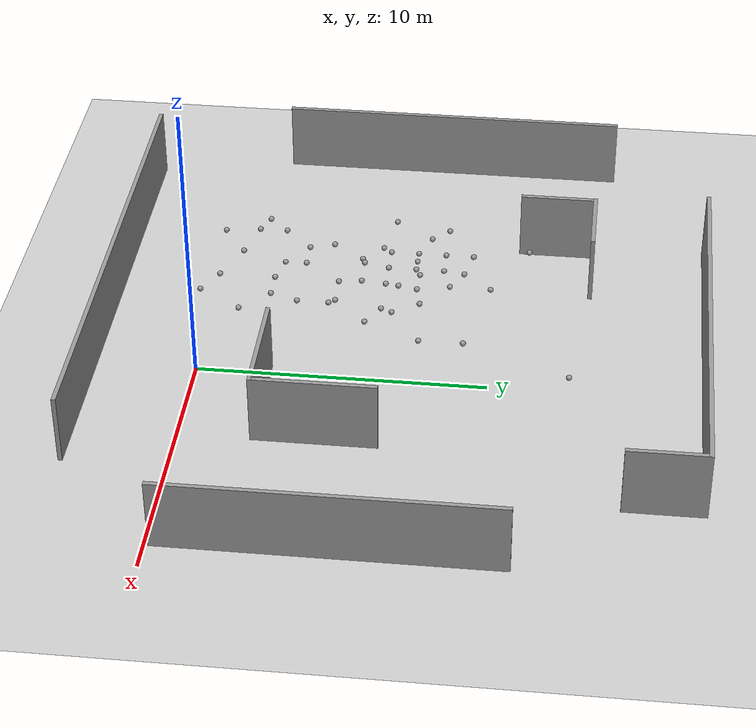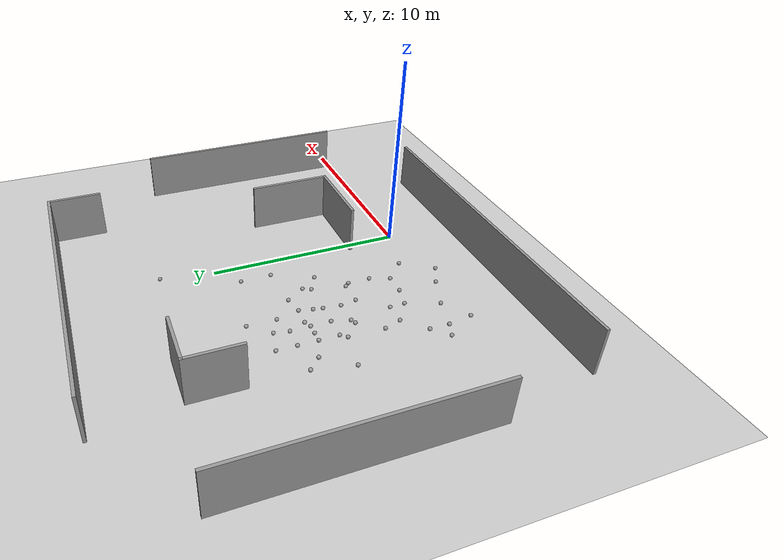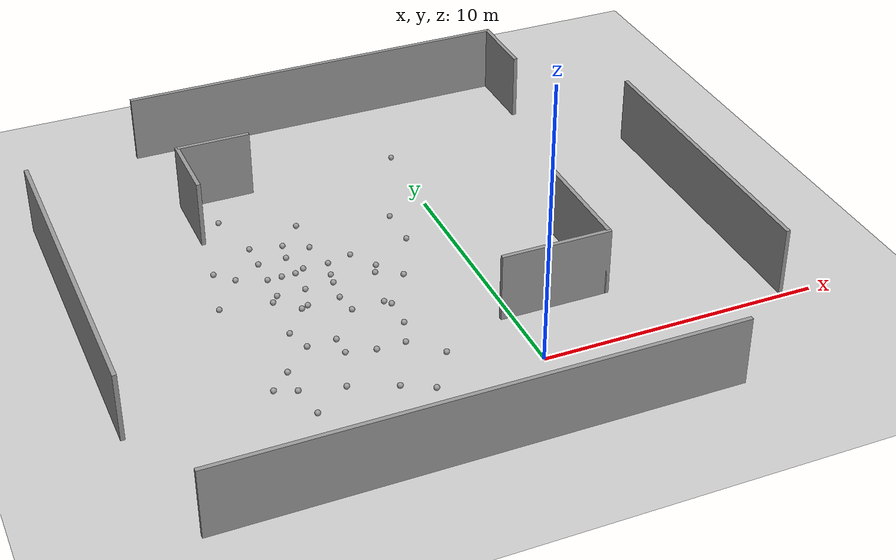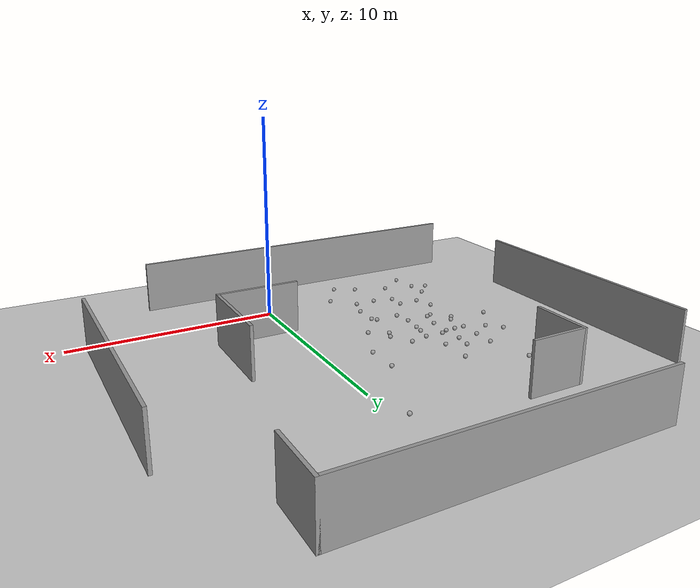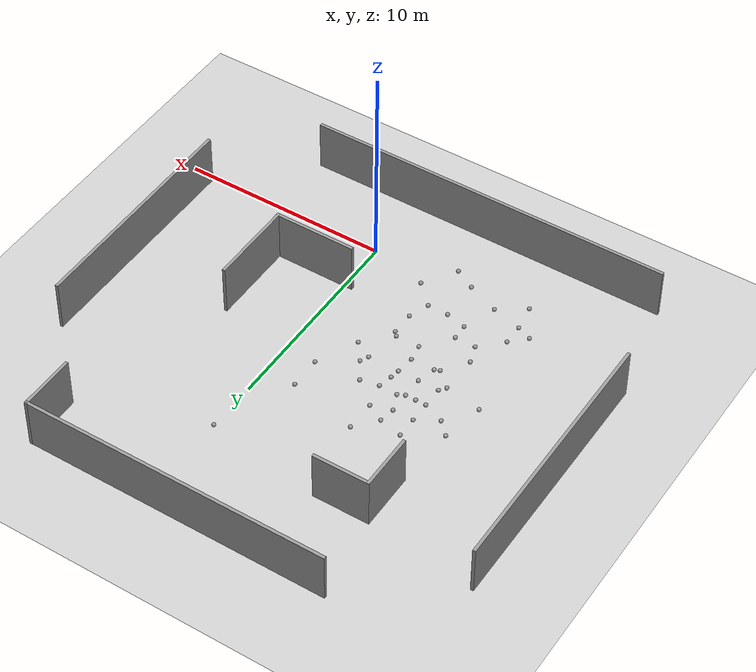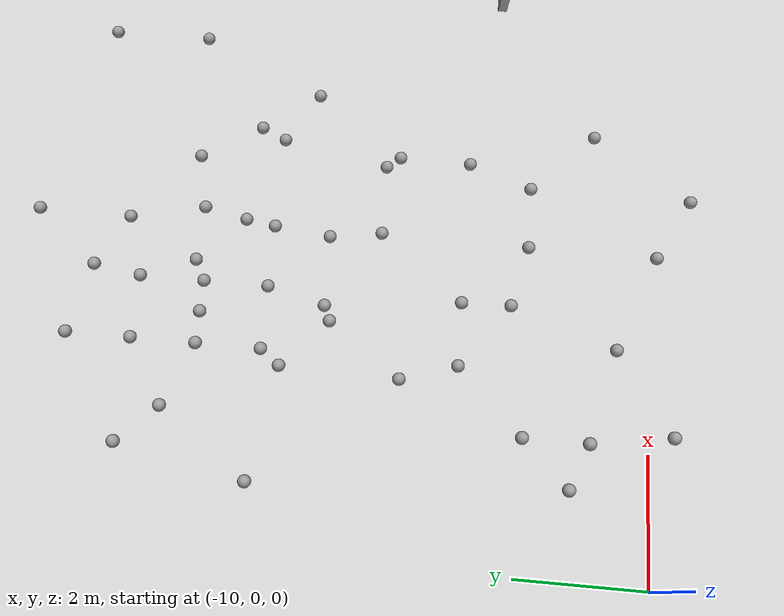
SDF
<sdf version="1.7">
 <world name="default">
  <light name="sun" type="directional">
   <pose>0 0 10 0 -0 0</pose>
   <diffuse>0.8 0.8 0.8 1</diffuse>
   <specular>0.2 0.2 0.2 1</specular>
   <attenuation>
    <range>1000</range>
    <constant>0.9</constant>
    <linear>0.01</linear>
    <quadratic>0.001</quadratic>
   </attenuation>
   <direction>-0.5 0.1 -0.9</direction>
   <spot><inner_angle>0</inner_angle><outer_angle>0</outer_angle><falloff>0</falloff></spot>
  </light>
  <model name="ground_plane">
   <static>1</static>
   <link name="link">
    <collision name="collision">
     <geometry><plane><normal>0 0 1</normal><size>100 100</size></plane></geometry>
     <surface>
      <contact><collide_bitmask>65535</collide_bitmask></contact>
      <friction><ode><mu>100</mu><mu2>50</mu2></ode></friction>
     </surface>
    </collision>
    <visual name="visual">
     <cast_shadows>0</cast_shadows>
     <geometry><plane><normal>0 0 1</normal><size>100 100</size></plane></geometry>
     <material>
      <script><uri>file://media/materials/scripts/gazebo.material</uri><name>Gazebo/Grey</name></script>
     </material>
    </visual>
   </link>
  </model>
  <gravity>0 0 -9.8</gravity>
  <magnetic_field>6e-06 2.3e-05 -4.2e-05</magnetic_field>
  <atmosphere type="adiabatic"/>
  <physics type="ode">
   <max_step_size>0.001</max_step_size>
   <real_time_factor>1</real_time_factor>
   <real_time_update_rate>1000</real_time_update_rate>
  </physics>
  <scene><ambient>0.4 0.4 0.4 1</ambient><background>0.7 0.7 0.7 1</background><shadows>1</shadows></scene>
  <audio><device>default</device></audio>
  <spherical_coordinates>
   <surface_model>EARTH_WGS84</surface_model>
   <latitude_deg>0</latitude_deg>
   <longitude_deg>0</longitude_deg>
   <elevation>0</elevation>
   <heading_deg>0</heading_deg>
  </spherical_coordinates>
  <model name="Wallworld">
   <pose>-2.25057 6.92757 0 0 -0 0</pose>
   <link name="Wall_17">
    <collision name="Wall_17_Collision">
     <geometry><box><size>17.75 0.15 2.5</size></box></geometry>
     <pose>0 0 1.25 0 -0 0</pose>
    </collision>
    <visual name="Wall_17_Visual">
     <pose>0 0 1.25 0 -0 0</pose>
     <geometry><box><size>17.75 0.15 2.5</size></box></geometry>
     <material>
      <script><uri>file://media/materials/scripts/gazebo.material</uri><name>Gazebo/Grey</name></script>
      <ambient>1 1 1 1</ambient>
     </material>
     <meta><layer>0</layer></meta>
    </visual>
    <pose>-1.33606 -10.4255 0 0 -0 0</pose>
   </link>
   <link name="Wall_19">
    <collision name="Wall_19_Collision">
     <geometry><box><size>11.25 0.15 2.5</size></box></geometry>
     <pose>0 0 1.25 0 -0 0</pose>
    </collision>
    <visual name="Wall_19_Visual">
     <pose>0 0 1.25 0 -0 0</pose>
     <geometry><box><size>11.25 0.15 2.5</size></box></geometry>
     <material>
      <script><uri>file://media/materials/scripts/gazebo.material</uri><name>Gazebo/Grey</name></script>
      <ambient>1 1 1 1</ambient>
     </material>
     <meta><layer>0</layer></meta>
    </visual>
    <pose>11.2141 -1.14728 0 0 -0 -1.5708</pose>
   </link>
   <link name="Wall_21">
    <collision name="Wall_21_Collision">
     <geometry><box><size>4 0.15 2.5</size></box></geometry>
     <pose>0 0 1.25 0 -0 0</pose>
    </collision>
    <visual name="Wall_21_Visual">
     <pose>0 0 1.25 0 -0 0</pose>
     <geometry><box><size>4 0.15 2.5</size></box></geometry>
     <material>
      <script><uri>file://media/materials/scripts/gazebo.material</uri><name>Gazebo/Grey</name></script>
      <ambient>1 1 1 1</ambient>
     </material>
     <meta><layer>0</layer></meta>
    </visual>
    <pose>3.84841 -4.39577 0 0 -0 0</pose>
   </link>
   <link name="Wall_22">
    <collision name="Wall_22_Collision">
     <geometry><box><size>4.25 0.15 2.5</size></box></geometry>
     <pose>0 0 1.25 0 -0 0</pose>
    </collision>
    <visual name="Wall_22_Visual">
     <pose>0 0 1.25 0 -0 0</pose>
     <geometry><box><size>4.25 0.15 2.5</size></box></geometry>
     <material>
      <script><uri>file://media/materials/scripts/gazebo.material</uri><name>Gazebo/Grey</name></script>
      <ambient>1 1 1 1</ambient>
     </material>
     <meta><layer>0</layer></meta>
    </visual>
    <pose>5.77341 -2.34577 0 0 -0 1.5708</pose>
   </link>
   <link name="Wall_24">
    <collision name="Wall_24_Collision">
     <geometry><box><size>12.5 0.15 2.5</size></box></geometry>
     <pose>0 0 1.25 0 -0 0</pose>
    </collision>
    <visual name="Wall_24_Visual">
     <pose>0 0 1.25 0 -0 0</pose>
     <geometry><box><size>12.5 0.15 2.5</size></box></geometry>
     <material>
      <script><uri>file://media/materials/scripts/gazebo.material</uri><name>Gazebo/Grey</name></script>
      <ambient>1 1 1 1</ambient>
     </material>
     <meta><layer>0</layer></meta>
    </visual>
    <pose>-11.2141 0.745498 0 0 -0 -1.5708</pose>
   </link>
   <link name="Wall_26">
    <collision name="Wall_26_Collision">
     <geometry><box><size>14.75 0.15 2.5</size></box></geometry>
     <pose>0 0 1.25 0 -0 0</pose>
    </collision>
    <visual name="Wall_26_Visual">
     <pose>0 0 1.25 0 -0 0</pose>
     <geometry><box><size>14.75 0.15 2.5</size></box></geometry>
     <material>
      <script><uri>file://media/materials/scripts/gazebo.material</uri><name>Gazebo/Grey</name></script>
      <ambient>1 1 1 1</ambient>
     </material>
     <meta><layer>0</layer></meta>
    </visual>
    <pose>0.787656 10.4255 0 0 -0 0</pose>
   </link>
   <link name="Wall_27">
    <collision name="Wall_27_Collision">
     <geometry><box><size>2.75 0.15 2.5</size></box></geometry>
     <pose>0 0 1.25 0 -0 0</pose>
    </collision>
    <visual name="Wall_27_Visual">
     <pose>0 0 1.25 0 -0 0</pose>
     <geometry><box><size>2.75 0.15 2.5</size></box></geometry>
     <material>
      <script><uri>file://media/materials/scripts/gazebo.material</uri><name>Gazebo/Grey</name></script>
      <ambient>1 1 1 1</ambient>
     </material>
     <meta><layer>0</layer></meta>
    </visual>
    <pose>8.08766 9.1255 0 0 -0 -1.5708</pose>
   </link>
   <link name="Wall_29">
    <collision name="Wall_29_Collision">
     <geometry><box><size>2.75 0.15 2.5</size></box></geometry>
     <pose>0 0 1.25 0 -0 0</pose>
    </collision>
    <visual name="Wall_29_Visual">
     <pose>0 0 1.25 0 -0 0</pose>
     <geometry><box><size>2.75 0.15 2.5</size></box></geometry>
     <material>
      <script><uri>file://media/materials/scripts/gazebo.material</uri><name>Gazebo/Grey</name></script>
      <ambient>1 1 1 1</ambient>
     </material>
     <meta><layer>0</layer></meta>
    </visual>
    <pose>-5.94275 5.05311 0 0 -0 1.5708</pose>
   </link>
   <link name="Wall_30">
    <collision name="Wall_30_Collision">
     <geometry><box><size>2.75 0.15 2.5</size></box></geometry>
     <pose>0 0 1.25 0 -0 0</pose>
    </collision>
    <visual name="Wall_30_Visual">
     <pose>0 0 1.25 0 -0 0</pose>
     <geometry><box><size>2.75 0.15 2.5</size></box></geometry>
     <material>
      <script><uri>file://media/materials/scripts/gazebo.material</uri><name>Gazebo/Grey</name></script>
      <ambient>1 1 1 1</ambient>
     </material>
     <meta><layer>0</layer></meta>
    </visual>
    <pose>-4.64275 6.35311 0 0 -0 0</pose>
   </link>
   <static>1</static>
  </model>
  <model name="0.1unit_sphere">
   <link name="link">
    <inertial>
     <mass>1</mass>
     <inertia><ixx>0.1</ixx><ixy>0</ixy><ixz>0</ixz><iyy>0.1</iyy><iyz>0</iyz><izz>0.1</izz></inertia>
    </inertial>
    <visual name="visual">
     <geometry><sphere><radius>0.1</radius></sphere></geometry>
     <material>
      <script><name>Gazebo/Grey</name><uri>file://media/materials/scripts/gazebo.material</uri></script>
      <shader type="pixel"><normal_map>__default__</normal_map></shader>
      <ambient>0.3 0.3 0.3 1</ambient>
      <diffuse>0.7 0.7 0.7 1</diffuse>
      <specular>0.01 0.01 0.01 1</specular>
      <emissive>0 0 0 1</emissive>
     </material>
    </visual>
    <collision name="collision">
     <geometry><sphere><radius>0.1</radius></sphere></geometry>
     <surface>
      <friction>
       <ode><mu>1</mu><mu2>1</mu2><fdir1>0 0 0</fdir1><slip1>0</slip1><slip2>0</slip2></ode>
       <torsional>
        <coefficient>1</coefficient>
        <patch_radius>0</patch_radius>
        <surface_radius>0</surface_radius>
        <use_patch_radius>1</use_patch_radius>
        <ode><slip>0</slip></ode>
       </torsional>
      </friction>
      <bounce><restitution_coefficient>0</restitution_coefficient><threshold>1e+06</threshold></bounce>
      <contact>
       <collide_without_contact>0</collide_without_contact>
       <collide_without_contact_bitmask>1</collide_without_contact_bitmask>
       <collide_bitmask>1</collide_bitmask>
       <ode>
        <soft_cfm>0</soft_cfm>
        <soft_erp>0.2</soft_erp>
        <kp>1e+13</kp>
        <kd>1</kd>
        <max_vel>0.01</max_vel>
        <min_depth>0</min_depth>
       </ode>
       <bullet>
        <split_impulse>1</split_impulse>
        <split_impulse_penetration_threshold>-0.01</split_impulse_penetration_threshold>
        <soft_cfm>0</soft_cfm>
        <soft_erp>0.2</soft_erp>
        <kp>1e+13</kp>
        <kd>1</kd>
       </bullet>
      </contact>
     </surface>
    </collision>
   </link>
   <static>0</static>
   <pose>-5.10007 5.12136 0.5 0 -0 0</pose>
  </model>
  <model name="0.1unit_sphere_clone">
   <link name="link">
    <inertial>
     <mass>1</mass>
     <inertia><ixx>0.1</ixx><ixy>0</ixy><ixz>0</ixz><iyy>0.1</iyy><iyz>0</iyz><izz>0.1</izz></inertia>
    </inertial>
    <visual name="visual">
     <geometry><sphere><radius>0.1</radius></sphere></geometry>
     <material>
      <script><name>Gazebo/Grey</name><uri>file://media/materials/scripts/gazebo.material</uri></script>
      <shader type="pixel"><normal_map>__default__</normal_map></shader>
      <ambient>0.3 0.3 0.3 1</ambient>
      <diffuse>0.7 0.7 0.7 1</diffuse>
      <specular>0.01 0.01 0.01 1</specular>
      <emissive>0 0 0 1</emissive>
     </material>
    </visual>
    <collision name="collision">
     <geometry><sphere><radius>0.1</radius></sphere></geometry>
     <surface>
      <friction>
       <ode><mu>1</mu><mu2>1</mu2><fdir1>0 0 0</fdir1><slip1>0</slip1><slip2>0</slip2></ode>
       <torsional>
        <coefficient>1</coefficient>
        <patch_radius>0</patch_radius>
        <surface_radius>0</surface_radius>
        <use_patch_radius>1</use_patch_radius>
        <ode><slip>0</slip></ode>
       </torsional>
      </friction>
      <bounce><restitution_coefficient>0</restitution_coefficient><threshold>1e+06</threshold></bounce>
      <contact>
       <collide_without_contact>0</collide_without_contact>
       <collide_without_contact_bitmask>1</collide_without_contact_bitmask>
       <collide_bitmask>1</collide_bitmask>
       <ode>
        <soft_cfm>0</soft_cfm>
        <soft_erp>0.2</soft_erp>
        <kp>1e+13</kp>
        <kd>1</kd>
        <max_vel>0.01</max_vel>
        <min_depth>0</min_depth>
       </ode>
       <bullet>
        <split_impulse>1</split_impulse>
        <split_impulse_penetration_threshold>-0.01</split_impulse_penetration_threshold>
        <soft_cfm>0</soft_cfm>
        <soft_erp>0.2</soft_erp>
        <kp>1e+13</kp>
        <kd>1</kd>
       </bullet>
      </contact>
     </surface>
    </collision>
   </link>
   <static>0</static>
   <pose>-5.66593 7.16766 0.5 0 -0 0</pose>
  </model>
  <model name="0.1unit_sphere_clone_0">
   <link name="link">
    <inertial>
     <mass>1</mass>
     <inertia><ixx>0.1</ixx><ixy>0</ixy><ixz>0</ixz><iyy>0.1</iyy><iyz>0</iyz><izz>0.1</izz></inertia>
    </inertial>
    <visual name="visual">
     <geometry><sphere><radius>0.1</radius></sphere></geometry>
     <material>
      <script><name>Gazebo/Grey</name><uri>file://media/materials/scripts/gazebo.material</uri></script>
      <shader type="pixel"><normal_map>__default__</normal_map></shader>
      <ambient>0.3 0.3 0.3 1</ambient>
      <diffuse>0.7 0.7 0.7 1</diffuse>
      <specular>0.01 0.01 0.01 1</specular>
      <emissive>0 0 0 1</emissive>
     </material>
    </visual>
    <collision name="collision">
     <geometry><sphere><radius>0.1</radius></sphere></geometry>
     <surface>
      <friction>
       <ode><mu>1</mu><mu2>1</mu2><fdir1>0 0 0</fdir1><slip1>0</slip1><slip2>0</slip2></ode>
       <torsional>
        <coefficient>1</coefficient>
        <patch_radius>0</patch_radius>
        <surface_radius>0</surface_radius>
        <use_patch_radius>1</use_patch_radius>
        <ode><slip>0</slip></ode>
       </torsional>
      </friction>
      <bounce><restitution_coefficient>0</restitution_coefficient><threshold>1e+06</threshold></bounce>
      <contact>
       <collide_without_contact>0</collide_without_contact>
       <collide_without_contact_bitmask>1</collide_without_contact_bitmask>
       <collide_bitmask>1</collide_bitmask>
       <ode>
        <soft_cfm>0</soft_cfm>
        <soft_erp>0.2</soft_erp>
        <kp>1e+13</kp>
        <kd>1</kd>
        <max_vel>0.01</max_vel>
        <min_depth>0</min_depth>
       </ode>
       <bullet>
        <split_impulse>1</split_impulse>
        <split_impulse_penetration_threshold>-0.01</split_impulse_penetration_threshold>
        <soft_cfm>0</soft_cfm>
        <soft_erp>0.2</soft_erp>
        <kp>1e+13</kp>
        <kd>1</kd>
       </bullet>
      </contact>
     </surface>
    </collision>
   </link>
   <static>0</static>
   <pose>-2.64217 5.51446 0.5 0 -0 0</pose>
  </model>
  <model name="0.1unit_sphere_clone_1">
   <link name="link">
    <inertial>
     <mass>1</mass>
     <inertia><ixx>0.1</ixx><ixy>0</ixy><ixz>0</ixz><iyy>0.1</iyy><iyz>0</iyz><izz>0.1</izz></inertia>
    </inertial>
    <visual name="visual">
     <geometry><sphere><radius>0.1</radius></sphere></geometry>
     <material>
      <script><name>Gazebo/Grey</name><uri>file://media/materials/scripts/gazebo.material</uri></script>
      <shader type="pixel"><normal_map>__default__</normal_map></shader>
      <ambient>0.3 0.3 0.3 1</ambient>
      <diffuse>0.7 0.7 0.7 1</diffuse>
      <specular>0.01 0.01 0.01 1</specular>
      <emissive>0 0 0 1</emissive>
     </material>
    </visual>
    <collision name="collision">
     <geometry><sphere><radius>0.1</radius></sphere></geometry>
     <surface>
      <friction>
       <ode><mu>1</mu><mu2>1</mu2><fdir1>0 0 0</fdir1><slip1>0</slip1><slip2>0</slip2></ode>
       <torsional>
        <coefficient>1</coefficient>
        <patch_radius>0</patch_radius>
        <surface_radius>0</surface_radius>
        <use_patch_radius>1</use_patch_radius>
        <ode><slip>0</slip></ode>
       </torsional>
      </friction>
      <bounce><restitution_coefficient>0</restitution_coefficient><threshold>1e+06</threshold></bounce>
      <contact>
       <collide_without_contact>0</collide_without_contact>
       <collide_without_contact_bitmask>1</collide_without_contact_bitmask>
       <collide_bitmask>1</collide_bitmask>
       <ode>
        <soft_cfm>0</soft_cfm>
        <soft_erp>0.2</soft_erp>
        <kp>1e+13</kp>
        <kd>1</kd>
        <max_vel>0.01</max_vel>
        <min_depth>0</min_depth>
       </ode>
       <bullet>
        <split_impulse>1</split_impulse>
        <split_impulse_penetration_threshold>-0.01</split_impulse_penetration_threshold>
        <soft_cfm>0</soft_cfm>
        <soft_erp>0.2</soft_erp>
        <kp>1e+13</kp>
        <kd>1</kd>
       </bullet>
      </contact>
     </surface>
    </collision>
   </link>
   <static>0</static>
   <pose>-3.89813 7.32606 0.5 0 -0 0</pose>
  </model>
  <model name="0.1unit_sphere_clone_2">
   <link name="link">
    <inertial>
     <mass>1</mass>
     <inertia><ixx>0.1</ixx><ixy>0</ixy><ixz>0</ixz><iyy>0.1</iyy><iyz>0</iyz><izz>0.1</izz></inertia>
    </inertial>
    <visual name="visual">
     <geometry><sphere><radius>0.1</radius></sphere></geometry>
     <material>
      <script><name>Gazebo/Grey</name><uri>file://media/materials/scripts/gazebo.material</uri></script>
      <shader type="pixel"><normal_map>__default__</normal_map></shader>
      <ambient>0.3 0.3 0.3 1</ambient>
      <diffuse>0.7 0.7 0.7 1</diffuse>
      <specular>0.01 0.01 0.01 1</specular>
      <emissive>0 0 0 1</emissive>
     </material>
    </visual>
    <collision name="collision">
     <geometry><sphere><radius>0.1</radius></sphere></geometry>
     <surface>
      <friction>
       <ode><mu>1</mu><mu2>1</mu2><fdir1>0 0 0</fdir1><slip1>0</slip1><slip2>0</slip2></ode>
       <torsional>
        <coefficient>1</coefficient>
        <patch_radius>0</patch_radius>
        <surface_radius>0</surface_radius>
        <use_patch_radius>1</use_patch_radius>
        <ode><slip>0</slip></ode>
       </torsional>
      </friction>
      <bounce><restitution_coefficient>0</restitution_coefficient><threshold>1e+06</threshold></bounce>
      <contact>
       <collide_without_contact>0</collide_without_contact>
       <collide_without_contact_bitmask>1</collide_without_contact_bitmask>
       <collide_bitmask>1</collide_bitmask>
       <ode>
        <soft_cfm>0</soft_cfm>
        <soft_erp>0.2</soft_erp>
        <kp>1e+13</kp>
        <kd>1</kd>
        <max_vel>0.01</max_vel>
        <min_depth>0</min_depth>
       </ode>
       <bullet>
        <split_impulse>1</split_impulse>
        <split_impulse_penetration_threshold>-0.01</split_impulse_penetration_threshold>
        <soft_cfm>0</soft_cfm>
        <soft_erp>0.2</soft_erp>
        <kp>1e+13</kp>
        <kd>1</kd>
       </bullet>
      </contact>
     </surface>
    </collision>
   </link>
   <static>0</static>
   <pose>-5 6 0.5 0 -0 0</pose>
  </model>
  <model name="0.1unit_sphere_clone_3">
   <link name="link">
    <inertial>
     <mass>1</mass>
     <inertia><ixx>0.1</ixx><ixy>0</ixy><ixz>0</ixz><iyy>0.1</iyy><iyz>0</iyz><izz>0.1</izz></inertia>
    </inertial>
    <visual name="visual">
     <geometry><sphere><radius>0.1</radius></sphere></geometry>
     <material>
      <script><name>Gazebo/Grey</name><uri>file://media/materials/scripts/gazebo.material</uri></script>
      <shader type="pixel"><normal_map>__default__</normal_map></shader>
      <ambient>0.3 0.3 0.3 1</ambient>
      <diffuse>0.7 0.7 0.7 1</diffuse>
      <specular>0.01 0.01 0.01 1</specular>
      <emissive>0 0 0 1</emissive>
     </material>
    </visual>
    <collision name="collision">
     <geometry><sphere><radius>0.1</radius></sphere></geometry>
     <surface>
      <friction>
       <ode><mu>1</mu><mu2>1</mu2><fdir1>0 0 0</fdir1><slip1>0</slip1><slip2>0</slip2></ode>
       <torsional>
        <coefficient>1</coefficient>
        <patch_radius>0</patch_radius>
        <surface_radius>0</surface_radius>
        <use_patch_radius>1</use_patch_radius>
        <ode><slip>0</slip></ode>
       </torsional>
      </friction>
      <bounce><restitution_coefficient>0</restitution_coefficient><threshold>1e+06</threshold></bounce>
      <contact>
       <collide_without_contact>0</collide_without_contact>
       <collide_without_contact_bitmask>1</collide_without_contact_bitmask>
       <collide_bitmask>1</collide_bitmask>
       <ode>
        <soft_cfm>0</soft_cfm>
        <soft_erp>0.2</soft_erp>
        <kp>1e+13</kp>
        <kd>1</kd>
        <max_vel>0.01</max_vel>
        <min_depth>0</min_depth>
       </ode>
       <bullet>
        <split_impulse>1</split_impulse>
        <split_impulse_penetration_threshold>-0.01</split_impulse_penetration_threshold>
        <soft_cfm>0</soft_cfm>
        <soft_erp>0.2</soft_erp>
        <kp>1e+13</kp>
        <kd>1</kd>
       </bullet>
      </contact>
     </surface>
    </collision>
   </link>
   <static>0</static>
   <pose>-7.23602 5.69775 0.5 0 -0 0</pose>
  </model>
  <model name="0.1unit_sphere_clone_4">
   <link name="link">
    <inertial>
     <mass>1</mass>
     <inertia><ixx>0.1</ixx><ixy>0</ixy><ixz>0</ixz><iyy>0.1</iyy><iyz>0</iyz><izz>0.1</izz></inertia>
    </inertial>
    <visual name="visual">
     <geometry><sphere><radius>0.1</radius></sphere></geometry>
     <material>
      <script><name>Gazebo/Grey</name><uri>file://media/materials/scripts/gazebo.material</uri></script>
      <shader type="pixel"><normal_map>__default__</normal_map></shader>
      <ambient>0.3 0.3 0.3 1</ambient>
      <diffuse>0.7 0.7 0.7 1</diffuse>
      <specular>0.01 0.01 0.01 1</specular>
      <emissive>0 0 0 1</emissive>
     </material>
    </visual>
    <collision name="collision">
     <geometry><sphere><radius>0.1</radius></sphere></geometry>
     <surface>
      <friction>
       <ode><mu>1</mu><mu2>1</mu2><fdir1>0 0 0</fdir1><slip1>0</slip1><slip2>0</slip2></ode>
       <torsional>
        <coefficient>1</coefficient>
        <patch_radius>0</patch_radius>
        <surface_radius>0</surface_radius>
        <use_patch_radius>1</use_patch_radius>
        <ode><slip>0</slip></ode>
       </torsional>
      </friction>
      <bounce><restitution_coefficient>0</restitution_coefficient><threshold>1e+06</threshold></bounce>
      <contact>
       <collide_without_contact>0</collide_without_contact>
       <collide_without_contact_bitmask>1</collide_without_contact_bitmask>
       <collide_bitmask>1</collide_bitmask>
       <ode>
        <soft_cfm>0</soft_cfm>
        <soft_erp>0.2</soft_erp>
        <kp>1e+13</kp>
        <kd>1</kd>
        <max_vel>0.01</max_vel>
        <min_depth>0</min_depth>
       </ode>
       <bullet>
        <split_impulse>1</split_impulse>
        <split_impulse_penetration_threshold>-0.01</split_impulse_penetration_threshold>
        <soft_cfm>0</soft_cfm>
        <soft_erp>0.2</soft_erp>
        <kp>1e+13</kp>
        <kd>1</kd>
       </bullet>
      </contact>
     </surface>
    </collision>
   </link>
   <static>0</static>
   <pose>-6 6 0.5 0 -0 0</pose>
  </model>
  <model name="0.1unit_sphere_clone_5">
   <link name="link">
    <inertial>
     <mass>1</mass>
     <inertia><ixx>0.1</ixx><ixy>0</ixy><ixz>0</ixz><iyy>0.1</iyy><iyz>0</iyz><izz>0.1</izz></inertia>
    </inertial>
    <visual name="visual">
     <geometry><sphere><radius>0.1</radius></sphere></geometry>
     <material>
      <script><name>Gazebo/Grey</name><uri>file://media/materials/scripts/gazebo.material</uri></script>
      <shader type="pixel"><normal_map>__default__</normal_map></shader>
      <ambient>0.3 0.3 0.3 1</ambient>
      <diffuse>0.7 0.7 0.7 1</diffuse>
      <specular>0.01 0.01 0.01 1</specular>
      <emissive>0 0 0 1</emissive>
     </material>
    </visual>
    <collision name="collision">
     <geometry><sphere><radius>0.1</radius></sphere></geometry>
     <surface>
      <friction>
       <ode><mu>1</mu><mu2>1</mu2><fdir1>0 0 0</fdir1><slip1>0</slip1><slip2>0</slip2></ode>
       <torsional>
        <coefficient>1</coefficient>
        <patch_radius>0</patch_radius>
        <surface_radius>0</surface_radius>
        <use_patch_radius>1</use_patch_radius>
        <ode><slip>0</slip></ode>
       </torsional>
      </friction>
      <bounce><restitution_coefficient>0</restitution_coefficient><threshold>1e+06</threshold></bounce>
      <contact>
       <collide_without_contact>0</collide_without_contact>
       <collide_without_contact_bitmask>1</collide_without_contact_bitmask>
       <collide_bitmask>1</collide_bitmask>
       <ode>
        <soft_cfm>0</soft_cfm>
        <soft_erp>0.2</soft_erp>
        <kp>1e+13</kp>
        <kd>1</kd>
        <max_vel>0.01</max_vel>
        <min_depth>0</min_depth>
       </ode>
       <bullet>
        <split_impulse>1</split_impulse>
        <split_impulse_penetration_threshold>-0.01</split_impulse_penetration_threshold>
        <soft_cfm>0</soft_cfm>
        <soft_erp>0.2</soft_erp>
        <kp>1e+13</kp>
        <kd>1</kd>
       </bullet>
      </contact>
     </surface>
    </collision>
   </link>
   <static>0</static>
   <pose>-7 7 0.5 0 -0 0</pose>
  </model>
  <model name="0.1unit_sphere_clone_6">
   <link name="link">
    <inertial>
     <mass>1</mass>
     <inertia><ixx>0.1</ixx><ixy>0</ixy><ixz>0</ixz><iyy>0.1</iyy><iyz>0</iyz><izz>0.1</izz></inertia>
    </inertial>
    <visual name="visual">
     <geometry><sphere><radius>0.1</radius></sphere></geometry>
     <material>
      <script><name>Gazebo/Grey</name><uri>file://media/materials/scripts/gazebo.material</uri></script>
      <shader type="pixel"><normal_map>__default__</normal_map></shader>
      <ambient>0.3 0.3 0.3 1</ambient>
      <diffuse>0.7 0.7 0.7 1</diffuse>
      <specular>0.01 0.01 0.01 1</specular>
      <emissive>0 0 0 1</emissive>
     </material>
    </visual>
    <collision name="collision">
     <geometry><sphere><radius>0.1</radius></sphere></geometry>
     <surface>
      <friction>
       <ode><mu>1</mu><mu2>1</mu2><fdir1>0 0 0</fdir1><slip1>0</slip1><slip2>0</slip2></ode>
       <torsional>
        <coefficient>1</coefficient>
        <patch_radius>0</patch_radius>
        <surface_radius>0</surface_radius>
        <use_patch_radius>1</use_patch_radius>
        <ode><slip>0</slip></ode>
       </torsional>
      </friction>
      <bounce><restitution_coefficient>0</restitution_coefficient><threshold>1e+06</threshold></bounce>
      <contact>
       <collide_without_contact>0</collide_without_contact>
       <collide_without_contact_bitmask>1</collide_without_contact_bitmask>
       <collide_bitmask>1</collide_bitmask>
       <ode>
        <soft_cfm>0</soft_cfm>
        <soft_erp>0.2</soft_erp>
        <kp>1e+13</kp>
        <kd>1</kd>
        <max_vel>0.01</max_vel>
        <min_depth>0</min_depth>
       </ode>
       <bullet>
        <split_impulse>1</split_impulse>
        <split_impulse_penetration_threshold>-0.01</split_impulse_penetration_threshold>
        <soft_cfm>0</soft_cfm>
        <soft_erp>0.2</soft_erp>
        <kp>1e+13</kp>
        <kd>1</kd>
       </bullet>
      </contact>
     </surface>
    </collision>
   </link>
   <static>0</static>
   <pose>-7 6 0.5 0 -0 0</pose>
  </model>
  <model name="0.1unit_sphere_clone_7">
   <link name="link">
    <inertial>
     <mass>1</mass>
     <inertia><ixx>0.1</ixx><ixy>0</ixy><ixz>0</ixz><iyy>0.1</iyy><iyz>0</iyz><izz>0.1</izz></inertia>
    </inertial>
    <visual name="visual">
     <geometry><sphere><radius>0.1</radius></sphere></geometry>
     <material>
      <script><name>Gazebo/Grey</name><uri>file://media/materials/scripts/gazebo.material</uri></script>
      <shader type="pixel"><normal_map>__default__</normal_map></shader>
      <ambient>0.3 0.3 0.3 1</ambient>
      <diffuse>0.7 0.7 0.7 1</diffuse>
      <specular>0.01 0.01 0.01 1</specular>
      <emissive>0 0 0 1</emissive>
     </material>
    </visual>
    <collision name="collision">
     <geometry><sphere><radius>0.1</radius></sphere></geometry>
     <surface>
      <friction>
       <ode><mu>1</mu><mu2>1</mu2><fdir1>0 0 0</fdir1><slip1>0</slip1><slip2>0</slip2></ode>
       <torsional>
        <coefficient>1</coefficient>
        <patch_radius>0</patch_radius>
        <surface_radius>0</surface_radius>
        <use_patch_radius>1</use_patch_radius>
        <ode><slip>0</slip></ode>
       </torsional>
      </friction>
      <bounce><restitution_coefficient>0</restitution_coefficient><threshold>1e+06</threshold></bounce>
      <contact>
       <collide_without_contact>0</collide_without_contact>
       <collide_without_contact_bitmask>1</collide_without_contact_bitmask>
       <collide_bitmask>1</collide_bitmask>
       <ode>
        <soft_cfm>0</soft_cfm>
        <soft_erp>0.2</soft_erp>
        <kp>1e+13</kp>
        <kd>1</kd>
        <max_vel>0.01</max_vel>
        <min_depth>0</min_depth>
       </ode>
       <bullet>
        <split_impulse>1</split_impulse>
        <split_impulse_penetration_threshold>-0.01</split_impulse_penetration_threshold>
        <soft_cfm>0</soft_cfm>
        <soft_erp>0.2</soft_erp>
        <kp>1e+13</kp>
        <kd>1</kd>
       </bullet>
      </contact>
     </surface>
    </collision>
   </link>
   <static>0</static>
   <pose>-6 7 0.5 0 -0 0</pose>
  </model>
  <model name="0.1unit_sphere_clone_8">
   <link name="link">
    <inertial>
     <mass>1</mass>
     <inertia><ixx>0.1</ixx><ixy>0</ixy><ixz>0</ixz><iyy>0.1</iyy><iyz>0</iyz><izz>0.1</izz></inertia>
    </inertial>
    <visual name="visual">
     <geometry><sphere><radius>0.1</radius></sphere></geometry>
     <material>
      <script><name>Gazebo/Grey</name><uri>file://media/materials/scripts/gazebo.material</uri></script>
      <shader type="pixel"><normal_map>__default__</normal_map></shader>
      <ambient>0.3 0.3 0.3 1</ambient>
      <diffuse>0.7 0.7 0.7 1</diffuse>
      <specular>0.01 0.01 0.01 1</specular>
      <emissive>0 0 0 1</emissive>
     </material>
    </visual>
    <collision name="collision">
     <geometry><sphere><radius>0.1</radius></sphere></geometry>
     <surface>
      <friction>
       <ode><mu>1</mu><mu2>1</mu2><fdir1>0 0 0</fdir1><slip1>0</slip1><slip2>0</slip2></ode>
       <torsional>
        <coefficient>1</coefficient>
        <patch_radius>0</patch_radius>
        <surface_radius>0</surface_radius>
        <use_patch_radius>1</use_patch_radius>
        <ode><slip>0</slip></ode>
       </torsional>
      </friction>
      <bounce><restitution_coefficient>0</restitution_coefficient><threshold>1e+06</threshold></bounce>
      <contact>
       <collide_without_contact>0</collide_without_contact>
       <collide_without_contact_bitmask>1</collide_without_contact_bitmask>
       <collide_bitmask>1</collide_bitmask>
       <ode>
        <soft_cfm>0</soft_cfm>
        <soft_erp>0.2</soft_erp>
        <kp>1e+13</kp>
        <kd>1</kd>
        <max_vel>0.01</max_vel>
        <min_depth>0</min_depth>
       </ode>
       <bullet>
        <split_impulse>1</split_impulse>
        <split_impulse_penetration_threshold>-0.01</split_impulse_penetration_threshold>
        <soft_cfm>0</soft_cfm>
        <soft_erp>0.2</soft_erp>
        <kp>1e+13</kp>
        <kd>1</kd>
       </bullet>
      </contact>
     </surface>
    </collision>
   </link>
   <static>0</static>
   <pose>-7.2839 3.87287 0.5 0 -0 0</pose>
  </model>
  <model name="0.1unit_sphere_clone_9">
   <link name="link">
    <inertial>
     <mass>1</mass>
     <inertia><ixx>0.1</ixx><ixy>0</ixy><ixz>0</ixz><iyy>0.1</iyy><iyz>0</iyz><izz>0.1</izz></inertia>
    </inertial>
    <visual name="visual">
     <geometry><sphere><radius>0.1</radius></sphere></geometry>
     <material>
      <script><name>Gazebo/Grey</name><uri>file://media/materials/scripts/gazebo.material</uri></script>
      <shader type="pixel"><normal_map>__default__</normal_map></shader>
      <ambient>0.3 0.3 0.3 1</ambient>
      <diffuse>0.7 0.7 0.7 1</diffuse>
      <specular>0.01 0.01 0.01 1</specular>
      <emissive>0 0 0 1</emissive>
     </material>
    </visual>
    <collision name="collision">
     <geometry><sphere><radius>0.1</radius></sphere></geometry>
     <surface>
      <friction>
       <ode><mu>1</mu><mu2>1</mu2><fdir1>0 0 0</fdir1><slip1>0</slip1><slip2>0</slip2></ode>
       <torsional>
        <coefficient>1</coefficient>
        <patch_radius>0</patch_radius>
        <surface_radius>0</surface_radius>
        <use_patch_radius>1</use_patch_radius>
        <ode><slip>0</slip></ode>
       </torsional>
      </friction>
      <bounce><restitution_coefficient>0</restitution_coefficient><threshold>1e+06</threshold></bounce>
      <contact>
       <collide_without_contact>0</collide_without_contact>
       <collide_without_contact_bitmask>1</collide_without_contact_bitmask>
       <collide_bitmask>1</collide_bitmask>
       <ode>
        <soft_cfm>0</soft_cfm>
        <soft_erp>0.2</soft_erp>
        <kp>1e+13</kp>
        <kd>1</kd>
        <max_vel>0.01</max_vel>
        <min_depth>0</min_depth>
       </ode>
       <bullet>
        <split_impulse>1</split_impulse>
        <split_impulse_penetration_threshold>-0.01</split_impulse_penetration_threshold>
        <soft_cfm>0</soft_cfm>
        <soft_erp>0.2</soft_erp>
        <kp>1e+13</kp>
        <kd>1</kd>
       </bullet>
      </contact>
     </surface>
    </collision>
   </link>
   <static>0</static>
   <pose>-6.47229 5 0.5 0 -0 0</pose>
  </model>
  <model name="0.1unit_sphere_clone_10">
   <link name="link">
    <inertial>
     <mass>1</mass>
     <inertia><ixx>0.1</ixx><ixy>0</ixy><ixz>0</ixz><iyy>0.1</iyy><iyz>0</iyz><izz>0.1</izz></inertia>
    </inertial>
    <visual name="visual">
     <geometry><sphere><radius>0.1</radius></sphere></geometry>
     <material>
      <script><name>Gazebo/Grey</name><uri>file://media/materials/scripts/gazebo.material</uri></script>
      <shader type="pixel"><normal_map>__default__</normal_map></shader>
      <ambient>0.3 0.3 0.3 1</ambient>
      <diffuse>0.7 0.7 0.7 1</diffuse>
      <specular>0.01 0.01 0.01 1</specular>
      <emissive>0 0 0 1</emissive>
     </material>
    </visual>
    <collision name="collision">
     <geometry><sphere><radius>0.1</radius></sphere></geometry>
     <surface>
      <friction>
       <ode><mu>1</mu><mu2>1</mu2><fdir1>0 0 0</fdir1><slip1>0</slip1><slip2>0</slip2></ode>
       <torsional>
        <coefficient>1</coefficient>
        <patch_radius>0</patch_radius>
        <surface_radius>0</surface_radius>
        <use_patch_radius>1</use_patch_radius>
        <ode><slip>0</slip></ode>
       </torsional>
      </friction>
      <bounce><restitution_coefficient>0</restitution_coefficient><threshold>1e+06</threshold></bounce>
      <contact>
       <collide_without_contact>0</collide_without_contact>
       <collide_without_contact_bitmask>1</collide_without_contact_bitmask>
       <collide_bitmask>1</collide_bitmask>
       <ode>
        <soft_cfm>0</soft_cfm>
        <soft_erp>0.2</soft_erp>
        <kp>1e+13</kp>
        <kd>1</kd>
        <max_vel>0.01</max_vel>
        <min_depth>0</min_depth>
       </ode>
       <bullet>
        <split_impulse>1</split_impulse>
        <split_impulse_penetration_threshold>-0.01</split_impulse_penetration_threshold>
        <soft_cfm>0</soft_cfm>
        <soft_erp>0.2</soft_erp>
        <kp>1e+13</kp>
        <kd>1</kd>
       </bullet>
      </contact>
     </surface>
    </collision>
   </link>
   <static>0</static>
   <pose>-6.49478 7 0.5 0 -0 0</pose>
  </model>
  <model name="0.1unit_sphere_clone_11">
   <link name="link">
    <inertial>
     <mass>1</mass>
     <inertia><ixx>0.1</ixx><ixy>0</ixy><ixz>0</ixz><iyy>0.1</iyy><iyz>0</iyz><izz>0.1</izz></inertia>
    </inertial>
    <visual name="visual">
     <geometry><sphere><radius>0.1</radius></sphere></geometry>
     <material>
      <script><name>Gazebo/Grey</name><uri>file://media/materials/scripts/gazebo.material</uri></script>
      <shader type="pixel"><normal_map>__default__</normal_map></shader>
      <ambient>0.3 0.3 0.3 1</ambient>
      <diffuse>0.7 0.7 0.7 1</diffuse>
      <specular>0.01 0.01 0.01 1</specular>
      <emissive>0 0 0 1</emissive>
     </material>
    </visual>
    <collision name="collision">
     <geometry><sphere><radius>0.1</radius></sphere></geometry>
     <surface>
      <friction>
       <ode><mu>1</mu><mu2>1</mu2><fdir1>0 0 0</fdir1><slip1>0</slip1><slip2>0</slip2></ode>
       <torsional>
        <coefficient>1</coefficient>
        <patch_radius>0</patch_radius>
        <surface_radius>0</surface_radius>
        <use_patch_radius>1</use_patch_radius>
        <ode><slip>0</slip></ode>
       </torsional>
      </friction>
      <bounce><restitution_coefficient>0</restitution_coefficient><threshold>1e+06</threshold></bounce>
      <contact>
       <collide_without_contact>0</collide_without_contact>
       <collide_without_contact_bitmask>1</collide_without_contact_bitmask>
       <collide_bitmask>1</collide_bitmask>
       <ode>
        <soft_cfm>0</soft_cfm>
        <soft_erp>0.2</soft_erp>
        <kp>1e+13</kp>
        <kd>1</kd>
        <max_vel>0.01</max_vel>
        <min_depth>0</min_depth>
       </ode>
       <bullet>
        <split_impulse>1</split_impulse>
        <split_impulse_penetration_threshold>-0.01</split_impulse_penetration_threshold>
        <soft_cfm>0</soft_cfm>
        <soft_erp>0.2</soft_erp>
        <kp>1e+13</kp>
        <kd>1</kd>
       </bullet>
      </contact>
     </surface>
    </collision>
   </link>
   <static>0</static>
   <pose>-6 8 0.5 0 -0 0</pose>
  </model>
  <model name="0.1unit_sphere_clone_12">
   <link name="link">
    <inertial>
     <mass>1</mass>
     <inertia><ixx>0.1</ixx><ixy>0</ixy><ixz>0</ixz><iyy>0.1</iyy><iyz>0</iyz><izz>0.1</izz></inertia>
    </inertial>
    <visual name="visual">
     <geometry><sphere><radius>0.1</radius></sphere></geometry>
     <material>
      <script><name>Gazebo/Grey</name><uri>file://media/materials/scripts/gazebo.material</uri></script>
      <shader type="pixel"><normal_map>__default__</normal_map></shader>
      <ambient>0.3 0.3 0.3 1</ambient>
      <diffuse>0.7 0.7 0.7 1</diffuse>
      <specular>0.01 0.01 0.01 1</specular>
      <emissive>0 0 0 1</emissive>
     </material>
    </visual>
    <collision name="collision">
     <geometry><sphere><radius>0.1</radius></sphere></geometry>
     <surface>
      <friction>
       <ode><mu>1</mu><mu2>1</mu2><fdir1>0 0 0</fdir1><slip1>0</slip1><slip2>0</slip2></ode>
       <torsional>
        <coefficient>1</coefficient>
        <patch_radius>0</patch_radius>
        <surface_radius>0</surface_radius>
        <use_patch_radius>1</use_patch_radius>
        <ode><slip>0</slip></ode>
       </torsional>
      </friction>
      <bounce><restitution_coefficient>0</restitution_coefficient><threshold>1e+06</threshold></bounce>
      <contact>
       <collide_without_contact>0</collide_without_contact>
       <collide_without_contact_bitmask>1</collide_without_contact_bitmask>
       <collide_bitmask>1</collide_bitmask>
       <ode>
        <soft_cfm>0</soft_cfm>
        <soft_erp>0.2</soft_erp>
        <kp>1e+13</kp>
        <kd>1</kd>
        <max_vel>0.01</max_vel>
        <min_depth>0</min_depth>
       </ode>
       <bullet>
        <split_impulse>1</split_impulse>
        <split_impulse_penetration_threshold>-0.01</split_impulse_penetration_threshold>
        <soft_cfm>0</soft_cfm>
        <soft_erp>0.2</soft_erp>
        <kp>1e+13</kp>
        <kd>1</kd>
       </bullet>
      </contact>
     </surface>
    </collision>
   </link>
   <static>0</static>
   <pose>-8.59317 8 0.5 0 -0 0</pose>
  </model>
  <model name="0.1unit_sphere_clone_13">
   <link name="link">
    <inertial>
     <mass>1</mass>
     <inertia><ixx>0.1</ixx><ixy>0</ixy><ixz>0</ixz><iyy>0.1</iyy><iyz>0</iyz><izz>0.1</izz></inertia>
    </inertial>
    <visual name="visual">
     <geometry><sphere><radius>0.1</radius></sphere></geometry>
     <material>
      <script><name>Gazebo/Grey</name><uri>file://media/materials/scripts/gazebo.material</uri></script>
      <shader type="pixel"><normal_map>__default__</normal_map></shader>
      <ambient>0.3 0.3 0.3 1</ambient>
      <diffuse>0.7 0.7 0.7 1</diffuse>
      <specular>0.01 0.01 0.01 1</specular>
      <emissive>0 0 0 1</emissive>
     </material>
    </visual>
    <collision name="collision">
     <geometry><sphere><radius>0.1</radius></sphere></geometry>
     <surface>
      <friction>
       <ode><mu>1</mu><mu2>1</mu2><fdir1>0 0 0</fdir1><slip1>0</slip1><slip2>0</slip2></ode>
       <torsional>
        <coefficient>1</coefficient>
        <patch_radius>0</patch_radius>
        <surface_radius>0</surface_radius>
        <use_patch_radius>1</use_patch_radius>
        <ode><slip>0</slip></ode>
       </torsional>
      </friction>
      <bounce><restitution_coefficient>0</restitution_coefficient><threshold>1e+06</threshold></bounce>
      <contact>
       <collide_without_contact>0</collide_without_contact>
       <collide_without_contact_bitmask>1</collide_without_contact_bitmask>
       <collide_bitmask>1</collide_bitmask>
       <ode>
        <soft_cfm>0</soft_cfm>
        <soft_erp>0.2</soft_erp>
        <kp>1e+13</kp>
        <kd>1</kd>
        <max_vel>0.01</max_vel>
        <min_depth>0</min_depth>
       </ode>
       <bullet>
        <split_impulse>1</split_impulse>
        <split_impulse_penetration_threshold>-0.01</split_impulse_penetration_threshold>
        <soft_cfm>0</soft_cfm>
        <soft_erp>0.2</soft_erp>
        <kp>1e+13</kp>
        <kd>1</kd>
       </bullet>
      </contact>
     </surface>
    </collision>
   </link>
   <static>0</static>
   <pose>-5.87568 8.7451 0.5 0 -0 0</pose>
  </model>
  <model name="0.1unit_sphere_clone_14">
   <link name="link">
    <inertial>
     <mass>1</mass>
     <inertia><ixx>0.1</ixx><ixy>0</ixy><ixz>0</ixz><iyy>0.1</iyy><iyz>0</iyz><izz>0.1</izz></inertia>
    </inertial>
    <visual name="visual">
     <geometry><sphere><radius>0.1</radius></sphere></geometry>
     <material>
      <script><name>Gazebo/Grey</name><uri>file://media/materials/scripts/gazebo.material</uri></script>
      <shader type="pixel"><normal_map>__default__</normal_map></shader>
      <ambient>0.3 0.3 0.3 1</ambient>
      <diffuse>0.7 0.7 0.7 1</diffuse>
      <specular>0.01 0.01 0.01 1</specular>
      <emissive>0 0 0 1</emissive>
     </material>
    </visual>
    <collision name="collision">
     <geometry><sphere><radius>0.1</radius></sphere></geometry>
     <surface>
      <friction>
       <ode><mu>1</mu><mu2>1</mu2><fdir1>0 0 0</fdir1><slip1>0</slip1><slip2>0</slip2></ode>
       <torsional>
        <coefficient>1</coefficient>
        <patch_radius>0</patch_radius>
        <surface_radius>0</surface_radius>
        <use_patch_radius>1</use_patch_radius>
        <ode><slip>0</slip></ode>
       </torsional>
      </friction>
      <bounce><restitution_coefficient>0</restitution_coefficient><threshold>1e+06</threshold></bounce>
      <contact>
       <collide_without_contact>0</collide_without_contact>
       <collide_without_contact_bitmask>1</collide_without_contact_bitmask>
       <collide_bitmask>1</collide_bitmask>
       <ode>
        <soft_cfm>0</soft_cfm>
        <soft_erp>0.2</soft_erp>
        <kp>1e+13</kp>
        <kd>1</kd>
        <max_vel>0.01</max_vel>
        <min_depth>0</min_depth>
       </ode>
       <bullet>
        <split_impulse>1</split_impulse>
        <split_impulse_penetration_threshold>-0.01</split_impulse_penetration_threshold>
        <soft_cfm>0</soft_cfm>
        <soft_erp>0.2</soft_erp>
        <kp>1e+13</kp>
        <kd>1</kd>
       </bullet>
      </contact>
     </surface>
    </collision>
   </link>
   <static>0</static>
   <pose>-7 7 0.5 0 -0 0</pose>
  </model>
  <model name="0.1unit_sphere_clone_15">
   <link name="link">
    <inertial>
     <mass>1</mass>
     <inertia><ixx>0.1</ixx><ixy>0</ixy><ixz>0</ixz><iyy>0.1</iyy><iyz>0</iyz><izz>0.1</izz></inertia>
    </inertial>
    <visual name="visual">
     <geometry><sphere><radius>0.1</radius></sphere></geometry>
     <material>
      <script><name>Gazebo/Grey</name><uri>file://media/materials/scripts/gazebo.material</uri></script>
      <shader type="pixel"><normal_map>__default__</normal_map></shader>
      <ambient>0.3 0.3 0.3 1</ambient>
      <diffuse>0.7 0.7 0.7 1</diffuse>
      <specular>0.01 0.01 0.01 1</specular>
      <emissive>0 0 0 1</emissive>
     </material>
    </visual>
    <collision name="collision">
     <geometry><sphere><radius>0.1</radius></sphere></geometry>
     <surface>
      <friction>
       <ode><mu>1</mu><mu2>1</mu2><fdir1>0 0 0</fdir1><slip1>0</slip1><slip2>0</slip2></ode>
       <torsional>
        <coefficient>1</coefficient>
        <patch_radius>0</patch_radius>
        <surface_radius>0</surface_radius>
        <use_patch_radius>1</use_patch_radius>
        <ode><slip>0</slip></ode>
       </torsional>
      </friction>
      <bounce><restitution_coefficient>0</restitution_coefficient><threshold>1e+06</threshold></bounce>
      <contact>
       <collide_without_contact>0</collide_without_contact>
       <collide_without_contact_bitmask>1</collide_without_contact_bitmask>
       <collide_bitmask>1</collide_bitmask>
       <ode>
        <soft_cfm>0</soft_cfm>
        <soft_erp>0.2</soft_erp>
        <kp>1e+13</kp>
        <kd>1</kd>
        <max_vel>0.01</max_vel>
        <min_depth>0</min_depth>
       </ode>
       <bullet>
        <split_impulse>1</split_impulse>
        <split_impulse_penetration_threshold>-0.01</split_impulse_penetration_threshold>
        <soft_cfm>0</soft_cfm>
        <soft_erp>0.2</soft_erp>
        <kp>1e+13</kp>
        <kd>1</kd>
       </bullet>
      </contact>
     </surface>
    </collision>
   </link>
   <static>0</static>
   <pose>-9 6 0.5 0 -0 0</pose>
  </model>
  <model name="0.1unit_sphere_clone_16">
   <link name="link">
    <inertial>
     <mass>1</mass>
     <inertia><ixx>0.1</ixx><ixy>0</ixy><ixz>0</ixz><iyy>0.1</iyy><iyz>0</iyz><izz>0.1</izz></inertia>
    </inertial>
    <visual name="visual">
     <geometry><sphere><radius>0.1</radius></sphere></geometry>
     <material>
      <script><name>Gazebo/Grey</name><uri>file://media/materials/scripts/gazebo.material</uri></script>
      <shader type="pixel"><normal_map>__default__</normal_map></shader>
      <ambient>0.3 0.3 0.3 1</ambient>
      <diffuse>0.7 0.7 0.7 1</diffuse>
      <specular>0.01 0.01 0.01 1</specular>
      <emissive>0 0 0 1</emissive>
     </material>
    </visual>
    <collision name="collision">
     <geometry><sphere><radius>0.1</radius></sphere></geometry>
     <surface>
      <friction>
       <ode><mu>1</mu><mu2>1</mu2><fdir1>0 0 0</fdir1><slip1>0</slip1><slip2>0</slip2></ode>
       <torsional>
        <coefficient>1</coefficient>
        <patch_radius>0</patch_radius>
        <surface_radius>0</surface_radius>
        <use_patch_radius>1</use_patch_radius>
        <ode><slip>0</slip></ode>
       </torsional>
      </friction>
      <bounce><restitution_coefficient>0</restitution_coefficient><threshold>1e+06</threshold></bounce>
      <contact>
       <collide_without_contact>0</collide_without_contact>
       <collide_without_contact_bitmask>1</collide_without_contact_bitmask>
       <collide_bitmask>1</collide_bitmask>
       <ode>
        <soft_cfm>0</soft_cfm>
        <soft_erp>0.2</soft_erp>
        <kp>1e+13</kp>
        <kd>1</kd>
        <max_vel>0.01</max_vel>
        <min_depth>0</min_depth>
       </ode>
       <bullet>
        <split_impulse>1</split_impulse>
        <split_impulse_penetration_threshold>-0.01</split_impulse_penetration_threshold>
        <soft_cfm>0</soft_cfm>
        <soft_erp>0.2</soft_erp>
        <kp>1e+13</kp>
        <kd>1</kd>
       </bullet>
      </contact>
     </surface>
    </collision>
   </link>
   <static>0</static>
   <pose>-8 7.40207 0.5 0 -0 0</pose>
  </model>
  <model name="0.1unit_sphere_clone_17">
   <link name="link">
    <inertial>
     <mass>1</mass>
     <inertia><ixx>0.1</ixx><ixy>0</ixy><ixz>0</ixz><iyy>0.1</iyy><iyz>0</iyz><izz>0.1</izz></inertia>
    </inertial>
    <visual name="visual">
     <geometry><sphere><radius>0.1</radius></sphere></geometry>
     <material>
      <script><name>Gazebo/Grey</name><uri>file://media/materials/scripts/gazebo.material</uri></script>
      <shader type="pixel"><normal_map>__default__</normal_map></shader>
      <ambient>0.3 0.3 0.3 1</ambient>
      <diffuse>0.7 0.7 0.7 1</diffuse>
      <specular>0.01 0.01 0.01 1</specular>
      <emissive>0 0 0 1</emissive>
     </material>
    </visual>
    <collision name="collision">
     <geometry><sphere><radius>0.1</radius></sphere></geometry>
     <surface>
      <friction>
       <ode><mu>1</mu><mu2>1</mu2><fdir1>0 0 0</fdir1><slip1>0</slip1><slip2>0</slip2></ode>
       <torsional>
        <coefficient>1</coefficient>
        <patch_radius>0</patch_radius>
        <surface_radius>0</surface_radius>
        <use_patch_radius>1</use_patch_radius>
        <ode><slip>0</slip></ode>
       </torsional>
      </friction>
      <bounce><restitution_coefficient>0</restitution_coefficient><threshold>1e+06</threshold></bounce>
      <contact>
       <collide_without_contact>0</collide_without_contact>
       <collide_without_contact_bitmask>1</collide_without_contact_bitmask>
       <collide_bitmask>1</collide_bitmask>
       <ode>
        <soft_cfm>0</soft_cfm>
        <soft_erp>0.2</soft_erp>
        <kp>1e+13</kp>
        <kd>1</kd>
        <max_vel>0.01</max_vel>
        <min_depth>0</min_depth>
       </ode>
       <bullet>
        <split_impulse>1</split_impulse>
        <split_impulse_penetration_threshold>-0.01</split_impulse_penetration_threshold>
        <soft_cfm>0</soft_cfm>
        <soft_erp>0.2</soft_erp>
        <kp>1e+13</kp>
        <kd>1</kd>
       </bullet>
      </contact>
     </surface>
    </collision>
   </link>
   <static>0</static>
   <pose>-7 9 0.5 0 -0 0</pose>
  </model>
  <model name="0.1unit_sphere_clone_18">
   <link name="link">
    <inertial>
     <mass>1</mass>
     <inertia><ixx>0.1</ixx><ixy>0</ixy><ixz>0</ixz><iyy>0.1</iyy><iyz>0</iyz><izz>0.1</izz></inertia>
    </inertial>
    <visual name="visual">
     <geometry><sphere><radius>0.1</radius></sphere></geometry>
     <material>
      <script><name>Gazebo/Grey</name><uri>file://media/materials/scripts/gazebo.material</uri></script>
      <shader type="pixel"><normal_map>__default__</normal_map></shader>
      <ambient>0.3 0.3 0.3 1</ambient>
      <diffuse>0.7 0.7 0.7 1</diffuse>
      <specular>0.01 0.01 0.01 1</specular>
      <emissive>0 0 0 1</emissive>
     </material>
    </visual>
    <collision name="collision">
     <geometry><sphere><radius>0.1</radius></sphere></geometry>
     <surface>
      <friction>
       <ode><mu>1</mu><mu2>1</mu2><fdir1>0 0 0</fdir1><slip1>0</slip1><slip2>0</slip2></ode>
       <torsional>
        <coefficient>1</coefficient>
        <patch_radius>0</patch_radius>
        <surface_radius>0</surface_radius>
        <use_patch_radius>1</use_patch_radius>
        <ode><slip>0</slip></ode>
       </torsional>
      </friction>
      <bounce><restitution_coefficient>0</restitution_coefficient><threshold>1e+06</threshold></bounce>
      <contact>
       <collide_without_contact>0</collide_without_contact>
       <collide_without_contact_bitmask>1</collide_without_contact_bitmask>
       <collide_bitmask>1</collide_bitmask>
       <ode>
        <soft_cfm>0</soft_cfm>
        <soft_erp>0.2</soft_erp>
        <kp>1e+13</kp>
        <kd>1</kd>
        <max_vel>0.01</max_vel>
        <min_depth>0</min_depth>
       </ode>
       <bullet>
        <split_impulse>1</split_impulse>
        <split_impulse_penetration_threshold>-0.01</split_impulse_penetration_threshold>
        <soft_cfm>0</soft_cfm>
        <soft_erp>0.2</soft_erp>
        <kp>1e+13</kp>
        <kd>1</kd>
       </bullet>
      </contact>
     </surface>
    </collision>
   </link>
   <static>0</static>
   <pose>-7 8 0.5 0 -0 0</pose>
  </model>
  <model name="0.1unit_sphere_clone_19">
   <link name="link">
    <inertial>
     <mass>1</mass>
     <inertia><ixx>0.1</ixx><ixy>0</ixy><ixz>0</ixz><iyy>0.1</iyy><iyz>0</iyz><izz>0.1</izz></inertia>
    </inertial>
    <visual name="visual">
     <geometry><sphere><radius>0.1</radius></sphere></geometry>
     <material>
      <script><name>Gazebo/Grey</name><uri>file://media/materials/scripts/gazebo.material</uri></script>
      <shader type="pixel"><normal_map>__default__</normal_map></shader>
      <ambient>0.3 0.3 0.3 1</ambient>
      <diffuse>0.7 0.7 0.7 1</diffuse>
      <specular>0.01 0.01 0.01 1</specular>
      <emissive>0 0 0 1</emissive>
     </material>
    </visual>
    <collision name="collision">
     <geometry><sphere><radius>0.1</radius></sphere></geometry>
     <surface>
      <friction>
       <ode><mu>1</mu><mu2>1</mu2><fdir1>0 0 0</fdir1><slip1>0</slip1><slip2>0</slip2></ode>
       <torsional>
        <coefficient>1</coefficient>
        <patch_radius>0</patch_radius>
        <surface_radius>0</surface_radius>
        <use_patch_radius>1</use_patch_radius>
        <ode><slip>0</slip></ode>
       </torsional>
      </friction>
      <bounce><restitution_coefficient>0</restitution_coefficient><threshold>1e+06</threshold></bounce>
      <contact>
       <collide_without_contact>0</collide_without_contact>
       <collide_without_contact_bitmask>1</collide_without_contact_bitmask>
       <collide_bitmask>1</collide_bitmask>
       <ode>
        <soft_cfm>0</soft_cfm>
        <soft_erp>0.2</soft_erp>
        <kp>1e+13</kp>
        <kd>1</kd>
        <max_vel>0.01</max_vel>
        <min_depth>0</min_depth>
       </ode>
       <bullet>
        <split_impulse>1</split_impulse>
        <split_impulse_penetration_threshold>-0.01</split_impulse_penetration_threshold>
        <soft_cfm>0</soft_cfm>
        <soft_erp>0.2</soft_erp>
        <kp>1e+13</kp>
        <kd>1</kd>
       </bullet>
      </contact>
     </surface>
    </collision>
   </link>
   <static>0</static>
   <pose>-4.92793 6.46164 0.5 0 -0 0</pose>
  </model>
  <model name="0.1unit_sphere_clone_20">
   <link name="link">
    <inertial>
     <mass>1</mass>
     <inertia><ixx>0.1</ixx><ixy>0</ixy><ixz>0</ixz><iyy>0.1</iyy><iyz>0</iyz><izz>0.1</izz></inertia>
    </inertial>
    <visual name="visual">
     <geometry><sphere><radius>0.1</radius></sphere></geometry>
     <material>
      <script><name>Gazebo/Grey</name><uri>file://media/materials/scripts/gazebo.material</uri></script>
      <shader type="pixel"><normal_map>__default__</normal_map></shader>
      <ambient>0.3 0.3 0.3 1</ambient>
      <diffuse>0.7 0.7 0.7 1</diffuse>
      <specular>0.01 0.01 0.01 1</specular>
      <emissive>0 0 0 1</emissive>
     </material>
    </visual>
    <collision name="collision">
     <geometry><sphere><radius>0.1</radius></sphere></geometry>
     <surface>
      <friction>
       <ode><mu>1</mu><mu2>1</mu2><fdir1>0 0 0</fdir1><slip1>0</slip1><slip2>0</slip2></ode>
       <torsional>
        <coefficient>1</coefficient>
        <patch_radius>0</patch_radius>
        <surface_radius>0</surface_radius>
        <use_patch_radius>1</use_patch_radius>
        <ode><slip>0</slip></ode>
       </torsional>
      </friction>
      <bounce><restitution_coefficient>0</restitution_coefficient><threshold>1e+06</threshold></bounce>
      <contact>
       <collide_without_contact>0</collide_without_contact>
       <collide_without_contact_bitmask>1</collide_without_contact_bitmask>
       <collide_bitmask>1</collide_bitmask>
       <ode>
        <soft_cfm>0</soft_cfm>
        <soft_erp>0.2</soft_erp>
        <kp>1e+13</kp>
        <kd>1</kd>
        <max_vel>0.01</max_vel>
        <min_depth>0</min_depth>
       </ode>
       <bullet>
        <split_impulse>1</split_impulse>
        <split_impulse_penetration_threshold>-0.01</split_impulse_penetration_threshold>
        <soft_cfm>0</soft_cfm>
        <soft_erp>0.2</soft_erp>
        <kp>1e+13</kp>
        <kd>1</kd>
       </bullet>
      </contact>
     </surface>
    </collision>
   </link>
   <static>0</static>
   <pose>-7.80227 -0.24423 0.5 0 -0 0</pose>
  </model>
  <model name="0.1unit_sphere_clone_21">
   <link name="link">
    <inertial>
     <mass>1</mass>
     <inertia><ixx>0.1</ixx><ixy>0</ixy><ixz>0</ixz><iyy>0.1</iyy><iyz>0</iyz><izz>0.1</izz></inertia>
    </inertial>
    <visual name="visual">
     <geometry><sphere><radius>0.1</radius></sphere></geometry>
     <material>
      <script><name>Gazebo/Grey</name><uri>file://media/materials/scripts/gazebo.material</uri></script>
      <shader type="pixel"><normal_map>__default__</normal_map></shader>
      <ambient>0.3 0.3 0.3 1</ambient>
      <diffuse>0.7 0.7 0.7 1</diffuse>
      <specular>0.01 0.01 0.01 1</specular>
      <emissive>0 0 0 1</emissive>
     </material>
    </visual>
    <collision name="collision">
     <geometry><sphere><radius>0.1</radius></sphere></geometry>
     <surface>
      <friction>
       <ode><mu>1</mu><mu2>1</mu2><fdir1>0 0 0</fdir1><slip1>0</slip1><slip2>0</slip2></ode>
       <torsional>
        <coefficient>1</coefficient>
        <patch_radius>0</patch_radius>
        <surface_radius>0</surface_radius>
        <use_patch_radius>1</use_patch_radius>
        <ode><slip>0</slip></ode>
       </torsional>
      </friction>
      <bounce><restitution_coefficient>0</restitution_coefficient><threshold>1e+06</threshold></bounce>
      <contact>
       <collide_without_contact>0</collide_without_contact>
       <collide_without_contact_bitmask>1</collide_without_contact_bitmask>
       <collide_bitmask>1</collide_bitmask>
       <ode>
        <soft_cfm>0</soft_cfm>
        <soft_erp>0.2</soft_erp>
        <kp>1e+13</kp>
        <kd>1</kd>
        <max_vel>0.01</max_vel>
        <min_depth>0</min_depth>
       </ode>
       <bullet>
        <split_impulse>1</split_impulse>
        <split_impulse_penetration_threshold>-0.01</split_impulse_penetration_threshold>
        <soft_cfm>0</soft_cfm>
        <soft_erp>0.2</soft_erp>
        <kp>1e+13</kp>
        <kd>1</kd>
       </bullet>
      </contact>
     </surface>
    </collision>
   </link>
   <static>0</static>
   <pose>-8.70134 1.29156 0.5 0 -0 0</pose>
  </model>
  <model name="0.1unit_sphere_clone_22">
   <link name="link">
    <inertial>
     <mass>1</mass>
     <inertia><ixx>0.1</ixx><ixy>0</ixy><ixz>0</ixz><iyy>0.1</iyy><iyz>0</iyz><izz>0.1</izz></inertia>
    </inertial>
    <visual name="visual">
     <geometry><sphere><radius>0.1</radius></sphere></geometry>
     <material>
      <script><name>Gazebo/Grey</name><uri>file://media/materials/scripts/gazebo.material</uri></script>
      <shader type="pixel"><normal_map>__default__</normal_map></shader>
      <ambient>0.3 0.3 0.3 1</ambient>
      <diffuse>0.7 0.7 0.7 1</diffuse>
      <specular>0.01 0.01 0.01 1</specular>
      <emissive>0 0 0 1</emissive>
     </material>
    </visual>
    <collision name="collision">
     <geometry><sphere><radius>0.1</radius></sphere></geometry>
     <surface>
      <friction>
       <ode><mu>1</mu><mu2>1</mu2><fdir1>0 0 0</fdir1><slip1>0</slip1><slip2>0</slip2></ode>
       <torsional>
        <coefficient>1</coefficient>
        <patch_radius>0</patch_radius>
        <surface_radius>0</surface_radius>
        <use_patch_radius>1</use_patch_radius>
        <ode><slip>0</slip></ode>
       </torsional>
      </friction>
      <bounce><restitution_coefficient>0</restitution_coefficient><threshold>1e+06</threshold></bounce>
      <contact>
       <collide_without_contact>0</collide_without_contact>
       <collide_without_contact_bitmask>1</collide_without_contact_bitmask>
       <collide_bitmask>1</collide_bitmask>
       <ode>
        <soft_cfm>0</soft_cfm>
        <soft_erp>0.2</soft_erp>
        <kp>1e+13</kp>
        <kd>1</kd>
        <max_vel>0.01</max_vel>
        <min_depth>0</min_depth>
       </ode>
       <bullet>
        <split_impulse>1</split_impulse>
        <split_impulse_penetration_threshold>-0.01</split_impulse_penetration_threshold>
        <soft_cfm>0</soft_cfm>
        <soft_erp>0.2</soft_erp>
        <kp>1e+13</kp>
        <kd>1</kd>
       </bullet>
      </contact>
     </surface>
    </collision>
   </link>
   <static>0</static>
   <pose>-6.54143 0.614011 0.5 0 -0 0</pose>
  </model>
  <model name="0.1unit_sphere_clone_23">
   <link name="link">
    <inertial>
     <mass>1</mass>
     <inertia><ixx>0.1</ixx><ixy>0</ixy><ixz>0</ixz><iyy>0.1</iyy><iyz>0</iyz><izz>0.1</izz></inertia>
    </inertial>
    <visual name="visual">
     <geometry><sphere><radius>0.1</radius></sphere></geometry>
     <material>
      <script><name>Gazebo/Grey</name><uri>file://media/materials/scripts/gazebo.material</uri></script>
      <shader type="pixel"><normal_map>__default__</normal_map></shader>
      <ambient>0.3 0.3 0.3 1</ambient>
      <diffuse>0.7 0.7 0.7 1</diffuse>
      <specular>0.01 0.01 0.01 1</specular>
      <emissive>0 0 0 1</emissive>
     </material>
    </visual>
    <collision name="collision">
     <geometry><sphere><radius>0.1</radius></sphere></geometry>
     <surface>
      <friction>
       <ode><mu>1</mu><mu2>1</mu2><fdir1>0 0 0</fdir1><slip1>0</slip1><slip2>0</slip2></ode>
       <torsional>
        <coefficient>1</coefficient>
        <patch_radius>0</patch_radius>
        <surface_radius>0</surface_radius>
        <use_patch_radius>1</use_patch_radius>
        <ode><slip>0</slip></ode>
       </torsional>
      </friction>
      <bounce><restitution_coefficient>0</restitution_coefficient><threshold>1e+06</threshold></bounce>
      <contact>
       <collide_without_contact>0</collide_without_contact>
       <collide_without_contact_bitmask>1</collide_without_contact_bitmask>
       <collide_bitmask>1</collide_bitmask>
       <ode>
        <soft_cfm>0</soft_cfm>
        <soft_erp>0.2</soft_erp>
        <kp>1e+13</kp>
        <kd>1</kd>
        <max_vel>0.01</max_vel>
        <min_depth>0</min_depth>
       </ode>
       <bullet>
        <split_impulse>1</split_impulse>
        <split_impulse_penetration_threshold>-0.01</split_impulse_penetration_threshold>
        <soft_cfm>0</soft_cfm>
        <soft_erp>0.2</soft_erp>
        <kp>1e+13</kp>
        <kd>1</kd>
       </bullet>
      </contact>
     </surface>
    </collision>
   </link>
   <static>0</static>
   <pose>-5.9783 2.23926 0.5 0 -0 0</pose>
  </model>
  <model name="0.1unit_sphere_clone_24">
   <link name="link">
    <inertial>
     <mass>1</mass>
     <inertia><ixx>0.1</ixx><ixy>0</ixy><ixz>0</ixz><iyy>0.1</iyy><iyz>0</iyz><izz>0.1</izz></inertia>
    </inertial>
    <visual name="visual">
     <geometry><sphere><radius>0.1</radius></sphere></geometry>
     <material>
      <script><name>Gazebo/Grey</name><uri>file://media/materials/scripts/gazebo.material</uri></script>
      <shader type="pixel"><normal_map>__default__</normal_map></shader>
      <ambient>0.3 0.3 0.3 1</ambient>
      <diffuse>0.7 0.7 0.7 1</diffuse>
      <specular>0.01 0.01 0.01 1</specular>
      <emissive>0 0 0 1</emissive>
     </material>
    </visual>
    <collision name="collision">
     <geometry><sphere><radius>0.1</radius></sphere></geometry>
     <surface>
      <friction>
       <ode><mu>1</mu><mu2>1</mu2><fdir1>0 0 0</fdir1><slip1>0</slip1><slip2>0</slip2></ode>
       <torsional>
        <coefficient>1</coefficient>
        <patch_radius>0</patch_radius>
        <surface_radius>0</surface_radius>
        <use_patch_radius>1</use_patch_radius>
        <ode><slip>0</slip></ode>
       </torsional>
      </friction>
      <bounce><restitution_coefficient>0</restitution_coefficient><threshold>1e+06</threshold></bounce>
      <contact>
       <collide_without_contact>0</collide_without_contact>
       <collide_without_contact_bitmask>1</collide_without_contact_bitmask>
       <collide_bitmask>1</collide_bitmask>
       <ode>
        <soft_cfm>0</soft_cfm>
        <soft_erp>0.2</soft_erp>
        <kp>1e+13</kp>
        <kd>1</kd>
        <max_vel>0.01</max_vel>
        <min_depth>0</min_depth>
       </ode>
       <bullet>
        <split_impulse>1</split_impulse>
        <split_impulse_penetration_threshold>-0.01</split_impulse_penetration_threshold>
        <soft_cfm>0</soft_cfm>
        <soft_erp>0.2</soft_erp>
        <kp>1e+13</kp>
        <kd>1</kd>
       </bullet>
      </contact>
     </surface>
    </collision>
   </link>
   <static>0</static>
   <pose>-4 2 0.5 0 -0 0</pose>
  </model>
  <model name="0.1unit_sphere_clone_25">
   <link name="link">
    <inertial>
     <mass>1</mass>
     <inertia><ixx>0.1</ixx><ixy>0</ixy><ixz>0</ixz><iyy>0.1</iyy><iyz>0</iyz><izz>0.1</izz></inertia>
    </inertial>
    <visual name="visual">
     <geometry><sphere><radius>0.1</radius></sphere></geometry>
     <material>
      <script><name>Gazebo/Grey</name><uri>file://media/materials/scripts/gazebo.material</uri></script>
      <shader type="pixel"><normal_map>__default__</normal_map></shader>
      <ambient>0.3 0.3 0.3 1</ambient>
      <diffuse>0.7 0.7 0.7 1</diffuse>
      <specular>0.01 0.01 0.01 1</specular>
      <emissive>0 0 0 1</emissive>
     </material>
    </visual>
    <collision name="collision">
     <geometry><sphere><radius>0.1</radius></sphere></geometry>
     <surface>
      <friction>
       <ode><mu>1</mu><mu2>1</mu2><fdir1>0 0 0</fdir1><slip1>0</slip1><slip2>0</slip2></ode>
       <torsional>
        <coefficient>1</coefficient>
        <patch_radius>0</patch_radius>
        <surface_radius>0</surface_radius>
        <use_patch_radius>1</use_patch_radius>
        <ode><slip>0</slip></ode>
       </torsional>
      </friction>
      <bounce><restitution_coefficient>0</restitution_coefficient><threshold>1e+06</threshold></bounce>
      <contact>
       <collide_without_contact>0</collide_without_contact>
       <collide_without_contact_bitmask>1</collide_without_contact_bitmask>
       <collide_bitmask>1</collide_bitmask>
       <ode>
        <soft_cfm>0</soft_cfm>
        <soft_erp>0.2</soft_erp>
        <kp>1e+13</kp>
        <kd>1</kd>
        <max_vel>0.01</max_vel>
        <min_depth>0</min_depth>
       </ode>
       <bullet>
        <split_impulse>1</split_impulse>
        <split_impulse_penetration_threshold>-0.01</split_impulse_penetration_threshold>
        <soft_cfm>0</soft_cfm>
        <soft_erp>0.2</soft_erp>
        <kp>1e+13</kp>
        <kd>1</kd>
       </bullet>
      </contact>
     </surface>
    </collision>
   </link>
   <static>0</static>
   <pose>-3.8257 4.32296 0.5 0 -0 0</pose>
  </model>
  <model name="0.1unit_sphere_clone_26">
   <link name="link">
    <inertial>
     <mass>1</mass>
     <inertia><ixx>0.1</ixx><ixy>0</ixy><ixz>0</ixz><iyy>0.1</iyy><iyz>0</iyz><izz>0.1</izz></inertia>
    </inertial>
    <visual name="visual">
     <geometry><sphere><radius>0.1</radius></sphere></geometry>
     <material>
      <script><name>Gazebo/Grey</name><uri>file://media/materials/scripts/gazebo.material</uri></script>
      <shader type="pixel"><normal_map>__default__</normal_map></shader>
      <ambient>0.3 0.3 0.3 1</ambient>
      <diffuse>0.7 0.7 0.7 1</diffuse>
      <specular>0.01 0.01 0.01 1</specular>
      <emissive>0 0 0 1</emissive>
     </material>
    </visual>
    <collision name="collision">
     <geometry><sphere><radius>0.1</radius></sphere></geometry>
     <surface>
      <friction>
       <ode><mu>1</mu><mu2>1</mu2><fdir1>0 0 0</fdir1><slip1>0</slip1><slip2>0</slip2></ode>
       <torsional>
        <coefficient>1</coefficient>
        <patch_radius>0</patch_radius>
        <surface_radius>0</surface_radius>
        <use_patch_radius>1</use_patch_radius>
        <ode><slip>0</slip></ode>
       </torsional>
      </friction>
      <bounce><restitution_coefficient>0</restitution_coefficient><threshold>1e+06</threshold></bounce>
      <contact>
       <collide_without_contact>0</collide_without_contact>
       <collide_without_contact_bitmask>1</collide_without_contact_bitmask>
       <collide_bitmask>1</collide_bitmask>
       <ode>
        <soft_cfm>0</soft_cfm>
        <soft_erp>0.2</soft_erp>
        <kp>1e+13</kp>
        <kd>1</kd>
        <max_vel>0.01</max_vel>
        <min_depth>0</min_depth>
       </ode>
       <bullet>
        <split_impulse>1</split_impulse>
        <split_impulse_penetration_threshold>-0.01</split_impulse_penetration_threshold>
        <soft_cfm>0</soft_cfm>
        <soft_erp>0.2</soft_erp>
        <kp>1e+13</kp>
        <kd>1</kd>
       </bullet>
      </contact>
     </surface>
    </collision>
   </link>
   <static>0</static>
   <pose>-6 3 0.5 0 -0 0</pose>
  </model>
  <model name="0.1unit_sphere_clone_27">
   <link name="link">
    <inertial>
     <mass>1</mass>
     <inertia><ixx>0.1</ixx><ixy>0</ixy><ixz>0</ixz><iyy>0.1</iyy><iyz>0</iyz><izz>0.1</izz></inertia>
    </inertial>
    <visual name="visual">
     <geometry><sphere><radius>0.1</radius></sphere></geometry>
     <material>
      <script><name>Gazebo/Grey</name><uri>file://media/materials/scripts/gazebo.material</uri></script>
      <shader type="pixel"><normal_map>__default__</normal_map></shader>
      <ambient>0.3 0.3 0.3 1</ambient>
      <diffuse>0.7 0.7 0.7 1</diffuse>
      <specular>0.01 0.01 0.01 1</specular>
      <emissive>0 0 0 1</emissive>
     </material>
    </visual>
    <collision name="collision">
     <geometry><sphere><radius>0.1</radius></sphere></geometry>
     <surface>
      <friction>
       <ode><mu>1</mu><mu2>1</mu2><fdir1>0 0 0</fdir1><slip1>0</slip1><slip2>0</slip2></ode>
       <torsional>
        <coefficient>1</coefficient>
        <patch_radius>0</patch_radius>
        <surface_radius>0</surface_radius>
        <use_patch_radius>1</use_patch_radius>
        <ode><slip>0</slip></ode>
       </torsional>
      </friction>
      <bounce><restitution_coefficient>0</restitution_coefficient><threshold>1e+06</threshold></bounce>
      <contact>
       <collide_without_contact>0</collide_without_contact>
       <collide_without_contact_bitmask>1</collide_without_contact_bitmask>
       <collide_bitmask>1</collide_bitmask>
       <ode>
        <soft_cfm>0</soft_cfm>
        <soft_erp>0.2</soft_erp>
        <kp>1e+13</kp>
        <kd>1</kd>
        <max_vel>0.01</max_vel>
        <min_depth>0</min_depth>
       </ode>
       <bullet>
        <split_impulse>1</split_impulse>
        <split_impulse_penetration_threshold>-0.01</split_impulse_penetration_threshold>
        <soft_cfm>0</soft_cfm>
        <soft_erp>0.2</soft_erp>
        <kp>1e+13</kp>
        <kd>1</kd>
       </bullet>
      </contact>
     </surface>
    </collision>
   </link>
   <static>0</static>
   <pose>-7 3 0.5 0 -0 0</pose>
  </model>
  <model name="0.1unit_sphere_clone_28">
   <link name="link">
    <inertial>
     <mass>1</mass>
     <inertia><ixx>0.1</ixx><ixy>0</ixy><ixz>0</ixz><iyy>0.1</iyy><iyz>0</iyz><izz>0.1</izz></inertia>
    </inertial>
    <visual name="visual">
     <geometry><sphere><radius>0.1</radius></sphere></geometry>
     <material>
      <script><name>Gazebo/Grey</name><uri>file://media/materials/scripts/gazebo.material</uri></script>
      <shader type="pixel"><normal_map>__default__</normal_map></shader>
      <ambient>0.3 0.3 0.3 1</ambient>
      <diffuse>0.7 0.7 0.7 1</diffuse>
      <specular>0.01 0.01 0.01 1</specular>
      <emissive>0 0 0 1</emissive>
     </material>
    </visual>
    <collision name="collision">
     <geometry><sphere><radius>0.1</radius></sphere></geometry>
     <surface>
      <friction>
       <ode><mu>1</mu><mu2>1</mu2><fdir1>0 0 0</fdir1><slip1>0</slip1><slip2>0</slip2></ode>
       <torsional>
        <coefficient>1</coefficient>
        <patch_radius>0</patch_radius>
        <surface_radius>0</surface_radius>
        <use_patch_radius>1</use_patch_radius>
        <ode><slip>0</slip></ode>
       </torsional>
      </friction>
      <bounce><restitution_coefficient>0</restitution_coefficient><threshold>1e+06</threshold></bounce>
      <contact>
       <collide_without_contact>0</collide_without_contact>
       <collide_without_contact_bitmask>1</collide_without_contact_bitmask>
       <collide_bitmask>1</collide_bitmask>
       <ode>
        <soft_cfm>0</soft_cfm>
        <soft_erp>0.2</soft_erp>
        <kp>1e+13</kp>
        <kd>1</kd>
        <max_vel>0.01</max_vel>
        <min_depth>0</min_depth>
       </ode>
       <bullet>
        <split_impulse>1</split_impulse>
        <split_impulse_penetration_threshold>-0.01</split_impulse_penetration_threshold>
        <soft_cfm>0</soft_cfm>
        <soft_erp>0.2</soft_erp>
        <kp>1e+13</kp>
        <kd>1</kd>
       </bullet>
      </contact>
     </surface>
    </collision>
   </link>
   <static>0</static>
   <pose>-8 2 0.5 0 -0 0</pose>
  </model>
  <model name="0.1unit_sphere_clone_29">
   <link name="link">
    <inertial>
     <mass>1</mass>
     <inertia><ixx>0.1</ixx><ixy>0</ixy><ixz>0</ixz><iyy>0.1</iyy><iyz>0</iyz><izz>0.1</izz></inertia>
    </inertial>
    <visual name="visual">
     <geometry><sphere><radius>0.1</radius></sphere></geometry>
     <material>
      <script><name>Gazebo/Grey</name><uri>file://media/materials/scripts/gazebo.material</uri></script>
      <shader type="pixel"><normal_map>__default__</normal_map></shader>
      <ambient>0.3 0.3 0.3 1</ambient>
      <diffuse>0.7 0.7 0.7 1</diffuse>
      <specular>0.01 0.01 0.01 1</specular>
      <emissive>0 0 0 1</emissive>
     </material>
    </visual>
    <collision name="collision">
     <geometry><sphere><radius>0.1</radius></sphere></geometry>
     <surface>
      <friction>
       <ode><mu>1</mu><mu2>1</mu2><fdir1>0 0 0</fdir1><slip1>0</slip1><slip2>0</slip2></ode>
       <torsional>
        <coefficient>1</coefficient>
        <patch_radius>0</patch_radius>
        <surface_radius>0</surface_radius>
        <use_patch_radius>1</use_patch_radius>
        <ode><slip>0</slip></ode>
       </torsional>
      </friction>
      <bounce><restitution_coefficient>0</restitution_coefficient><threshold>1e+06</threshold></bounce>
      <contact>
       <collide_without_contact>0</collide_without_contact>
       <collide_without_contact_bitmask>1</collide_without_contact_bitmask>
       <collide_bitmask>1</collide_bitmask>
       <ode>
        <soft_cfm>0</soft_cfm>
        <soft_erp>0.2</soft_erp>
        <kp>1e+13</kp>
        <kd>1</kd>
        <max_vel>0.01</max_vel>
        <min_depth>0</min_depth>
       </ode>
       <bullet>
        <split_impulse>1</split_impulse>
        <split_impulse_penetration_threshold>-0.01</split_impulse_penetration_threshold>
        <soft_cfm>0</soft_cfm>
        <soft_erp>0.2</soft_erp>
        <kp>1e+13</kp>
        <kd>1</kd>
       </bullet>
      </contact>
     </surface>
    </collision>
   </link>
   <static>0</static>
   <pose>-8 1 0.5 0 -0 0</pose>
  </model>
  <model name="0.1unit_sphere_clone_30">
   <link name="link">
    <inertial>
     <mass>1</mass>
     <inertia><ixx>0.1</ixx><ixy>0</ixy><ixz>0</ixz><iyy>0.1</iyy><iyz>0</iyz><izz>0.1</izz></inertia>
    </inertial>
    <visual name="visual">
     <geometry><sphere><radius>0.1</radius></sphere></geometry>
     <material>
      <script><name>Gazebo/Grey</name><uri>file://media/materials/scripts/gazebo.material</uri></script>
      <shader type="pixel"><normal_map>__default__</normal_map></shader>
      <ambient>0.3 0.3 0.3 1</ambient>
      <diffuse>0.7 0.7 0.7 1</diffuse>
      <specular>0.01 0.01 0.01 1</specular>
      <emissive>0 0 0 1</emissive>
     </material>
    </visual>
    <collision name="collision">
     <geometry><sphere><radius>0.1</radius></sphere></geometry>
     <surface>
      <friction>
       <ode><mu>1</mu><mu2>1</mu2><fdir1>0 0 0</fdir1><slip1>0</slip1><slip2>0</slip2></ode>
       <torsional>
        <coefficient>1</coefficient>
        <patch_radius>0</patch_radius>
        <surface_radius>0</surface_radius>
        <use_patch_radius>1</use_patch_radius>
        <ode><slip>0</slip></ode>
       </torsional>
      </friction>
      <bounce><restitution_coefficient>0</restitution_coefficient><threshold>1e+06</threshold></bounce>
      <contact>
       <collide_without_contact>0</collide_without_contact>
       <collide_without_contact_bitmask>1</collide_without_contact_bitmask>
       <collide_bitmask>1</collide_bitmask>
       <ode>
        <soft_cfm>0</soft_cfm>
        <soft_erp>0.2</soft_erp>
        <kp>1e+13</kp>
        <kd>1</kd>
        <max_vel>0.01</max_vel>
        <min_depth>0</min_depth>
       </ode>
       <bullet>
        <split_impulse>1</split_impulse>
        <split_impulse_penetration_threshold>-0.01</split_impulse_penetration_threshold>
        <soft_cfm>0</soft_cfm>
        <soft_erp>0.2</soft_erp>
        <kp>1e+13</kp>
        <kd>1</kd>
       </bullet>
      </contact>
     </surface>
    </collision>
   </link>
   <static>0</static>
   <pose>-5 0 0.5 0 -0 0</pose>
  </model>
  <model name="0.1unit_sphere_clone_31">
   <link name="link">
    <inertial>
     <mass>1</mass>
     <inertia><ixx>0.1</ixx><ixy>0</ixy><ixz>0</ixz><iyy>0.1</iyy><iyz>0</iyz><izz>0.1</izz></inertia>
    </inertial>
    <visual name="visual">
     <geometry><sphere><radius>0.1</radius></sphere></geometry>
     <material>
      <script><name>Gazebo/Grey</name><uri>file://media/materials/scripts/gazebo.material</uri></script>
      <shader type="pixel"><normal_map>__default__</normal_map></shader>
      <ambient>0.3 0.3 0.3 1</ambient>
      <diffuse>0.7 0.7 0.7 1</diffuse>
      <specular>0.01 0.01 0.01 1</specular>
      <emissive>0 0 0 1</emissive>
     </material>
    </visual>
    <collision name="collision">
     <geometry><sphere><radius>0.1</radius></sphere></geometry>
     <surface>
      <friction>
       <ode><mu>1</mu><mu2>1</mu2><fdir1>0 0 0</fdir1><slip1>0</slip1><slip2>0</slip2></ode>
       <torsional>
        <coefficient>1</coefficient>
        <patch_radius>0</patch_radius>
        <surface_radius>0</surface_radius>
        <use_patch_radius>1</use_patch_radius>
        <ode><slip>0</slip></ode>
       </torsional>
      </friction>
      <bounce><restitution_coefficient>0</restitution_coefficient><threshold>1e+06</threshold></bounce>
      <contact>
       <collide_without_contact>0</collide_without_contact>
       <collide_without_contact_bitmask>1</collide_without_contact_bitmask>
       <collide_bitmask>1</collide_bitmask>
       <ode>
        <soft_cfm>0</soft_cfm>
        <soft_erp>0.2</soft_erp>
        <kp>1e+13</kp>
        <kd>1</kd>
        <max_vel>0.01</max_vel>
        <min_depth>0</min_depth>
       </ode>
       <bullet>
        <split_impulse>1</split_impulse>
        <split_impulse_penetration_threshold>-0.01</split_impulse_penetration_threshold>
        <soft_cfm>0</soft_cfm>
        <soft_erp>0.2</soft_erp>
        <kp>1e+13</kp>
        <kd>1</kd>
       </bullet>
      </contact>
     </surface>
    </collision>
   </link>
   <static>0</static>
   <pose>-4 -0.538909 0.5 0 -0 0</pose>
  </model>
  <model name="0.1unit_sphere_clone_32">
   <link name="link">
    <inertial>
     <mass>1</mass>
     <inertia><ixx>0.1</ixx><ixy>0</ixy><ixz>0</ixz><iyy>0.1</iyy><iyz>0</iyz><izz>0.1</izz></inertia>
    </inertial>
    <visual name="visual">
     <geometry><sphere><radius>0.1</radius></sphere></geometry>
     <material>
      <script><name>Gazebo/Grey</name><uri>file://media/materials/scripts/gazebo.material</uri></script>
      <shader type="pixel"><normal_map>__default__</normal_map></shader>
      <ambient>0.3 0.3 0.3 1</ambient>
      <diffuse>0.7 0.7 0.7 1</diffuse>
      <specular>0.01 0.01 0.01 1</specular>
      <emissive>0 0 0 1</emissive>
     </material>
    </visual>
    <collision name="collision">
     <geometry><sphere><radius>0.1</radius></sphere></geometry>
     <surface>
      <friction>
       <ode><mu>1</mu><mu2>1</mu2><fdir1>0 0 0</fdir1><slip1>0</slip1><slip2>0</slip2></ode>
       <torsional>
        <coefficient>1</coefficient>
        <patch_radius>0</patch_radius>
        <surface_radius>0</surface_radius>
        <use_patch_radius>1</use_patch_radius>
        <ode><slip>0</slip></ode>
       </torsional>
      </friction>
      <bounce><restitution_coefficient>0</restitution_coefficient><threshold>1e+06</threshold></bounce>
      <contact>
       <collide_without_contact>0</collide_without_contact>
       <collide_without_contact_bitmask>1</collide_without_contact_bitmask>
       <collide_bitmask>1</collide_bitmask>
       <ode>
        <soft_cfm>0</soft_cfm>
        <soft_erp>0.2</soft_erp>
        <kp>1e+13</kp>
        <kd>1</kd>
        <max_vel>0.01</max_vel>
        <min_depth>0</min_depth>
       </ode>
       <bullet>
        <split_impulse>1</split_impulse>
        <split_impulse_penetration_threshold>-0.01</split_impulse_penetration_threshold>
        <soft_cfm>0</soft_cfm>
        <soft_erp>0.2</soft_erp>
        <kp>1e+13</kp>
        <kd>1</kd>
       </bullet>
      </contact>
     </surface>
    </collision>
   </link>
   <static>0</static>
   <pose>-3 1 0.5 0 -0 0</pose>
  </model>
  <model name="0.1unit_sphere_clone_33">
   <link name="link">
    <inertial>
     <mass>1</mass>
     <inertia><ixx>0.1</ixx><ixy>0</ixy><ixz>0</ixz><iyy>0.1</iyy><iyz>0</iyz><izz>0.1</izz></inertia>
    </inertial>
    <visual name="visual">
     <geometry><sphere><radius>0.1</radius></sphere></geometry>
     <material>
      <script><name>Gazebo/Grey</name><uri>file://media/materials/scripts/gazebo.material</uri></script>
      <shader type="pixel"><normal_map>__default__</normal_map></shader>
      <ambient>0.3 0.3 0.3 1</ambient>
      <diffuse>0.7 0.7 0.7 1</diffuse>
      <specular>0.01 0.01 0.01 1</specular>
      <emissive>0 0 0 1</emissive>
     </material>
    </visual>
    <collision name="collision">
     <geometry><sphere><radius>0.1</radius></sphere></geometry>
     <surface>
      <friction>
       <ode><mu>1</mu><mu2>1</mu2><fdir1>0 0 0</fdir1><slip1>0</slip1><slip2>0</slip2></ode>
       <torsional>
        <coefficient>1</coefficient>
        <patch_radius>0</patch_radius>
        <surface_radius>0</surface_radius>
        <use_patch_radius>1</use_patch_radius>
        <ode><slip>0</slip></ode>
       </torsional>
      </friction>
      <bounce><restitution_coefficient>0</restitution_coefficient><threshold>1e+06</threshold></bounce>
      <contact>
       <collide_without_contact>0</collide_without_contact>
       <collide_without_contact_bitmask>1</collide_without_contact_bitmask>
       <collide_bitmask>1</collide_bitmask>
       <ode>
        <soft_cfm>0</soft_cfm>
        <soft_erp>0.2</soft_erp>
        <kp>1e+13</kp>
        <kd>1</kd>
        <max_vel>0.01</max_vel>
        <min_depth>0</min_depth>
       </ode>
       <bullet>
        <split_impulse>1</split_impulse>
        <split_impulse_penetration_threshold>-0.01</split_impulse_penetration_threshold>
        <soft_cfm>0</soft_cfm>
        <soft_erp>0.2</soft_erp>
        <kp>1e+13</kp>
        <kd>1</kd>
       </bullet>
      </contact>
     </surface>
    </collision>
   </link>
   <static>0</static>
   <pose>-3 1 0.5 0 -0 0</pose>
  </model>
  <model name="0.1unit_sphere_clone_34">
   <link name="link">
    <inertial>
     <mass>1</mass>
     <inertia><ixx>0.1</ixx><ixy>0</ixy><ixz>0</ixz><iyy>0.1</iyy><iyz>0</iyz><izz>0.1</izz></inertia>
    </inertial>
    <visual name="visual">
     <geometry><sphere><radius>0.1</radius></sphere></geometry>
     <material>
      <script><name>Gazebo/Grey</name><uri>file://media/materials/scripts/gazebo.material</uri></script>
      <shader type="pixel"><normal_map>__default__</normal_map></shader>
      <ambient>0.3 0.3 0.3 1</ambient>
      <diffuse>0.7 0.7 0.7 1</diffuse>
      <specular>0.01 0.01 0.01 1</specular>
      <emissive>0 0 0 1</emissive>
     </material>
    </visual>
    <collision name="collision">
     <geometry><sphere><radius>0.1</radius></sphere></geometry>
     <surface>
      <friction>
       <ode><mu>1</mu><mu2>1</mu2><fdir1>0 0 0</fdir1><slip1>0</slip1><slip2>0</slip2></ode>
       <torsional>
        <coefficient>1</coefficient>
        <patch_radius>0</patch_radius>
        <surface_radius>0</surface_radius>
        <use_patch_radius>1</use_patch_radius>
        <ode><slip>0</slip></ode>
       </torsional>
      </friction>
      <bounce><restitution_coefficient>0</restitution_coefficient><threshold>1e+06</threshold></bounce>
      <contact>
       <collide_without_contact>0</collide_without_contact>
       <collide_without_contact_bitmask>1</collide_without_contact_bitmask>
       <collide_bitmask>1</collide_bitmask>
       <ode>
        <soft_cfm>0</soft_cfm>
        <soft_erp>0.2</soft_erp>
        <kp>1e+13</kp>
        <kd>1</kd>
        <max_vel>0.01</max_vel>
        <min_depth>0</min_depth>
       </ode>
       <bullet>
        <split_impulse>1</split_impulse>
        <split_impulse_penetration_threshold>-0.01</split_impulse_penetration_threshold>
        <soft_cfm>0</soft_cfm>
        <soft_erp>0.2</soft_erp>
        <kp>1e+13</kp>
        <kd>1</kd>
       </bullet>
      </contact>
     </surface>
    </collision>
   </link>
   <static>0</static>
   <pose>-3.4913 6 0.5 0 -0 0</pose>
  </model>
  <model name="0.1unit_sphere_clone_35">
   <link name="link">
    <inertial>
     <mass>1</mass>
     <inertia><ixx>0.1</ixx><ixy>0</ixy><ixz>0</ixz><iyy>0.1</iyy><iyz>0</iyz><izz>0.1</izz></inertia>
    </inertial>
    <visual name="visual">
     <geometry><sphere><radius>0.1</radius></sphere></geometry>
     <material>
      <script><name>Gazebo/Grey</name><uri>file://media/materials/scripts/gazebo.material</uri></script>
      <shader type="pixel"><normal_map>__default__</normal_map></shader>
      <ambient>0.3 0.3 0.3 1</ambient>
      <diffuse>0.7 0.7 0.7 1</diffuse>
      <specular>0.01 0.01 0.01 1</specular>
      <emissive>0 0 0 1</emissive>
     </material>
    </visual>
    <collision name="collision">
     <geometry><sphere><radius>0.1</radius></sphere></geometry>
     <surface>
      <friction>
       <ode><mu>1</mu><mu2>1</mu2><fdir1>0 0 0</fdir1><slip1>0</slip1><slip2>0</slip2></ode>
       <torsional>
        <coefficient>1</coefficient>
        <patch_radius>0</patch_radius>
        <surface_radius>0</surface_radius>
        <use_patch_radius>1</use_patch_radius>
        <ode><slip>0</slip></ode>
       </torsional>
      </friction>
      <bounce><restitution_coefficient>0</restitution_coefficient><threshold>1e+06</threshold></bounce>
      <contact>
       <collide_without_contact>0</collide_without_contact>
       <collide_without_contact_bitmask>1</collide_without_contact_bitmask>
       <collide_bitmask>1</collide_bitmask>
       <ode>
        <soft_cfm>0</soft_cfm>
        <soft_erp>0.2</soft_erp>
        <kp>1e+13</kp>
        <kd>1</kd>
        <max_vel>0.01</max_vel>
        <min_depth>0</min_depth>
       </ode>
       <bullet>
        <split_impulse>1</split_impulse>
        <split_impulse_penetration_threshold>-0.01</split_impulse_penetration_threshold>
        <soft_cfm>0</soft_cfm>
        <soft_erp>0.2</soft_erp>
        <kp>1e+13</kp>
        <kd>1</kd>
       </bullet>
      </contact>
     </surface>
    </collision>
   </link>
   <static>0</static>
   <pose>-3.30785 6.39267 0.5 0 -0 0</pose>
  </model>
  <model name="0.1unit_sphere_clone_36">
   <link name="link">
    <inertial>
     <mass>1</mass>
     <inertia><ixx>0.1</ixx><ixy>0</ixy><ixz>0</ixz><iyy>0.1</iyy><iyz>0</iyz><izz>0.1</izz></inertia>
    </inertial>
    <visual name="visual">
     <geometry><sphere><radius>0.1</radius></sphere></geometry>
     <material>
      <script><name>Gazebo/Grey</name><uri>file://media/materials/scripts/gazebo.material</uri></script>
      <shader type="pixel"><normal_map>__default__</normal_map></shader>
      <ambient>0.3 0.3 0.3 1</ambient>
      <diffuse>0.7 0.7 0.7 1</diffuse>
      <specular>0.01 0.01 0.01 1</specular>
      <emissive>0 0 0 1</emissive>
     </material>
    </visual>
    <collision name="collision">
     <geometry><sphere><radius>0.1</radius></sphere></geometry>
     <surface>
      <friction>
       <ode><mu>1</mu><mu2>1</mu2><fdir1>0 0 0</fdir1><slip1>0</slip1><slip2>0</slip2></ode>
       <torsional>
        <coefficient>1</coefficient>
        <patch_radius>0</patch_radius>
        <surface_radius>0</surface_radius>
        <use_patch_radius>1</use_patch_radius>
        <ode><slip>0</slip></ode>
       </torsional>
      </friction>
      <bounce><restitution_coefficient>0</restitution_coefficient><threshold>1e+06</threshold></bounce>
      <contact>
       <collide_without_contact>0</collide_without_contact>
       <collide_without_contact_bitmask>1</collide_without_contact_bitmask>
       <collide_bitmask>1</collide_bitmask>
       <ode>
        <soft_cfm>0</soft_cfm>
        <soft_erp>0.2</soft_erp>
        <kp>1e+13</kp>
        <kd>1</kd>
        <max_vel>0.01</max_vel>
        <min_depth>0</min_depth>
       </ode>
       <bullet>
        <split_impulse>1</split_impulse>
        <split_impulse_penetration_threshold>-0.01</split_impulse_penetration_threshold>
        <soft_cfm>0</soft_cfm>
        <soft_erp>0.2</soft_erp>
        <kp>1e+13</kp>
        <kd>1</kd>
       </bullet>
      </contact>
     </surface>
    </collision>
   </link>
   <static>0</static>
   <pose>-4.96927 4.31248 0.5 0 -0 0</pose>
  </model>
  <model name="0.1unit_sphere_clone_37">
   <link name="link">
    <inertial>
     <mass>1</mass>
     <inertia><ixx>0.1</ixx><ixy>0</ixy><ixz>0</ixz><iyy>0.1</iyy><iyz>0</iyz><izz>0.1</izz></inertia>
    </inertial>
    <visual name="visual">
     <geometry><sphere><radius>0.1</radius></sphere></geometry>
     <material>
      <script><name>Gazebo/Grey</name><uri>file://media/materials/scripts/gazebo.material</uri></script>
      <shader type="pixel"><normal_map>__default__</normal_map></shader>
      <ambient>0.3 0.3 0.3 1</ambient>
      <diffuse>0.7 0.7 0.7 1</diffuse>
      <specular>0.01 0.01 0.01 1</specular>
      <emissive>0 0 0 1</emissive>
     </material>
    </visual>
    <collision name="collision">
     <geometry><sphere><radius>0.1</radius></sphere></geometry>
     <surface>
      <friction>
       <ode><mu>1</mu><mu2>1</mu2><fdir1>0 0 0</fdir1><slip1>0</slip1><slip2>0</slip2></ode>
       <torsional>
        <coefficient>1</coefficient>
        <patch_radius>0</patch_radius>
        <surface_radius>0</surface_radius>
        <use_patch_radius>1</use_patch_radius>
        <ode><slip>0</slip></ode>
       </torsional>
      </friction>
      <bounce><restitution_coefficient>0</restitution_coefficient><threshold>1e+06</threshold></bounce>
      <contact>
       <collide_without_contact>0</collide_without_contact>
       <collide_without_contact_bitmask>1</collide_without_contact_bitmask>
       <collide_bitmask>1</collide_bitmask>
       <ode>
        <soft_cfm>0</soft_cfm>
        <soft_erp>0.2</soft_erp>
        <kp>1e+13</kp>
        <kd>1</kd>
        <max_vel>0.01</max_vel>
        <min_depth>0</min_depth>
       </ode>
       <bullet>
        <split_impulse>1</split_impulse>
        <split_impulse_penetration_threshold>-0.01</split_impulse_penetration_threshold>
        <soft_cfm>0</soft_cfm>
        <soft_erp>0.2</soft_erp>
        <kp>1e+13</kp>
        <kd>1</kd>
       </bullet>
      </contact>
     </surface>
    </collision>
   </link>
   <static>0</static>
   <pose>-5 2 0.5 0 -0 0</pose>
  </model>
  <model name="0.1unit_sphere_clone_38">
   <link name="link">
    <inertial>
     <mass>1</mass>
     <inertia><ixx>0.1</ixx><ixy>0</ixy><ixz>0</ixz><iyy>0.1</iyy><iyz>0</iyz><izz>0.1</izz></inertia>
    </inertial>
    <visual name="visual">
     <geometry><sphere><radius>0.1</radius></sphere></geometry>
     <material>
      <script><name>Gazebo/Grey</name><uri>file://media/materials/scripts/gazebo.material</uri></script>
      <shader type="pixel"><normal_map>__default__</normal_map></shader>
      <ambient>0.3 0.3 0.3 1</ambient>
      <diffuse>0.7 0.7 0.7 1</diffuse>
      <specular>0.01 0.01 0.01 1</specular>
      <emissive>0 0 0 1</emissive>
     </material>
    </visual>
    <collision name="collision">
     <geometry><sphere><radius>0.1</radius></sphere></geometry>
     <surface>
      <friction>
       <ode><mu>1</mu><mu2>1</mu2><fdir1>0 0 0</fdir1><slip1>0</slip1><slip2>0</slip2></ode>
       <torsional>
        <coefficient>1</coefficient>
        <patch_radius>0</patch_radius>
        <surface_radius>0</surface_radius>
        <use_patch_radius>1</use_patch_radius>
        <ode><slip>0</slip></ode>
       </torsional>
      </friction>
      <bounce><restitution_coefficient>0</restitution_coefficient><threshold>1e+06</threshold></bounce>
      <contact>
       <collide_without_contact>0</collide_without_contact>
       <collide_without_contact_bitmask>1</collide_without_contact_bitmask>
       <collide_bitmask>1</collide_bitmask>
       <ode>
        <soft_cfm>0</soft_cfm>
        <soft_erp>0.2</soft_erp>
        <kp>1e+13</kp>
        <kd>1</kd>
        <max_vel>0.01</max_vel>
        <min_depth>0</min_depth>
       </ode>
       <bullet>
        <split_impulse>1</split_impulse>
        <split_impulse_penetration_threshold>-0.01</split_impulse_penetration_threshold>
        <soft_cfm>0</soft_cfm>
        <soft_erp>0.2</soft_erp>
        <kp>1e+13</kp>
        <kd>1</kd>
       </bullet>
      </contact>
     </surface>
    </collision>
   </link>
   <static>0</static>
   <pose>-3.65389 2.98621 0.5 0 -0 0</pose>
  </model>
  <model name="0.1unit_sphere_clone_39">
   <link name="link">
    <inertial>
     <mass>1</mass>
     <inertia><ixx>0.1</ixx><ixy>0</ixy><ixz>0</ixz><iyy>0.1</iyy><iyz>0</iyz><izz>0.1</izz></inertia>
    </inertial>
    <visual name="visual">
     <geometry><sphere><radius>0.1</radius></sphere></geometry>
     <material>
      <script><name>Gazebo/Grey</name><uri>file://media/materials/scripts/gazebo.material</uri></script>
      <shader type="pixel"><normal_map>__default__</normal_map></shader>
      <ambient>0.3 0.3 0.3 1</ambient>
      <diffuse>0.7 0.7 0.7 1</diffuse>
      <specular>0.01 0.01 0.01 1</specular>
      <emissive>0 0 0 1</emissive>
     </material>
    </visual>
    <collision name="collision">
     <geometry><sphere><radius>0.1</radius></sphere></geometry>
     <surface>
      <friction>
       <ode><mu>1</mu><mu2>1</mu2><fdir1>0 0 0</fdir1><slip1>0</slip1><slip2>0</slip2></ode>
       <torsional>
        <coefficient>1</coefficient>
        <patch_radius>0</patch_radius>
        <surface_radius>0</surface_radius>
        <use_patch_radius>1</use_patch_radius>
        <ode><slip>0</slip></ode>
       </torsional>
      </friction>
      <bounce><restitution_coefficient>0</restitution_coefficient><threshold>1e+06</threshold></bounce>
      <contact>
       <collide_without_contact>0</collide_without_contact>
       <collide_without_contact_bitmask>1</collide_without_contact_bitmask>
       <collide_bitmask>1</collide_bitmask>
       <ode>
        <soft_cfm>0</soft_cfm>
        <soft_erp>0.2</soft_erp>
        <kp>1e+13</kp>
        <kd>1</kd>
        <max_vel>0.01</max_vel>
        <min_depth>0</min_depth>
       </ode>
       <bullet>
        <split_impulse>1</split_impulse>
        <split_impulse_penetration_threshold>-0.01</split_impulse_penetration_threshold>
        <soft_cfm>0</soft_cfm>
        <soft_erp>0.2</soft_erp>
        <kp>1e+13</kp>
        <kd>1</kd>
       </bullet>
      </contact>
     </surface>
    </collision>
   </link>
   <static>0</static>
   <pose>-3.64271 4.11071 0.5 0 -0 0</pose>
  </model>
  <model name="0.1unit_sphere_clone_40">
   <link name="link">
    <inertial>
     <mass>1</mass>
     <inertia><ixx>0.1</ixx><ixy>0</ixy><ixz>0</ixz><iyy>0.1</iyy><iyz>0</iyz><izz>0.1</izz></inertia>
    </inertial>
    <visual name="visual">
     <geometry><sphere><radius>0.1</radius></sphere></geometry>
     <material>
      <script><name>Gazebo/Grey</name><uri>file://media/materials/scripts/gazebo.material</uri></script>
      <shader type="pixel"><normal_map>__default__</normal_map></shader>
      <ambient>0.3 0.3 0.3 1</ambient>
      <diffuse>0.7 0.7 0.7 1</diffuse>
      <specular>0.01 0.01 0.01 1</specular>
      <emissive>0 0 0 1</emissive>
     </material>
    </visual>
    <collision name="collision">
     <geometry><sphere><radius>0.1</radius></sphere></geometry>
     <surface>
      <friction>
       <ode><mu>1</mu><mu2>1</mu2><fdir1>0 0 0</fdir1><slip1>0</slip1><slip2>0</slip2></ode>
       <torsional>
        <coefficient>1</coefficient>
        <patch_radius>0</patch_radius>
        <surface_radius>0</surface_radius>
        <use_patch_radius>1</use_patch_radius>
        <ode><slip>0</slip></ode>
       </torsional>
      </friction>
      <bounce><restitution_coefficient>0</restitution_coefficient><threshold>1e+06</threshold></bounce>
      <contact>
       <collide_without_contact>0</collide_without_contact>
       <collide_without_contact_bitmask>1</collide_without_contact_bitmask>
       <collide_bitmask>1</collide_bitmask>
       <ode>
        <soft_cfm>0</soft_cfm>
        <soft_erp>0.2</soft_erp>
        <kp>1e+13</kp>
        <kd>1</kd>
        <max_vel>0.01</max_vel>
        <min_depth>0</min_depth>
       </ode>
       <bullet>
        <split_impulse>1</split_impulse>
        <split_impulse_penetration_threshold>-0.01</split_impulse_penetration_threshold>
        <soft_cfm>0</soft_cfm>
        <soft_erp>0.2</soft_erp>
        <kp>1e+13</kp>
        <kd>1</kd>
       </bullet>
      </contact>
     </surface>
    </collision>
   </link>
   <static>0</static>
   <pose>-4.77696 7.13992 0.5 0 -0 0</pose>
  </model>
  <model name="0.1unit_sphere_clone_41">
   <link name="link">
    <inertial>
     <mass>1</mass>
     <inertia><ixx>0.1</ixx><ixy>0</ixy><ixz>0</ixz><iyy>0.1</iyy><iyz>0</iyz><izz>0.1</izz></inertia>
    </inertial>
    <visual name="visual">
     <geometry><sphere><radius>0.1</radius></sphere></geometry>
     <material>
      <script><name>Gazebo/Grey</name><uri>file://media/materials/scripts/gazebo.material</uri></script>
      <shader type="pixel"><normal_map>__default__</normal_map></shader>
      <ambient>0.3 0.3 0.3 1</ambient>
      <diffuse>0.7 0.7 0.7 1</diffuse>
      <specular>0.01 0.01 0.01 1</specular>
      <emissive>0 0 0 1</emissive>
     </material>
    </visual>
    <collision name="collision">
     <geometry><sphere><radius>0.1</radius></sphere></geometry>
     <surface>
      <friction>
       <ode><mu>1</mu><mu2>1</mu2><fdir1>0 0 0</fdir1><slip1>0</slip1><slip2>0</slip2></ode>
       <torsional>
        <coefficient>1</coefficient>
        <patch_radius>0</patch_radius>
        <surface_radius>0</surface_radius>
        <use_patch_radius>1</use_patch_radius>
        <ode><slip>0</slip></ode>
       </torsional>
      </friction>
      <bounce><restitution_coefficient>0</restitution_coefficient><threshold>1e+06</threshold></bounce>
      <contact>
       <collide_without_contact>0</collide_without_contact>
       <collide_without_contact_bitmask>1</collide_without_contact_bitmask>
       <collide_bitmask>1</collide_bitmask>
       <ode>
        <soft_cfm>0</soft_cfm>
        <soft_erp>0.2</soft_erp>
        <kp>1e+13</kp>
        <kd>1</kd>
        <max_vel>0.01</max_vel>
        <min_depth>0</min_depth>
       </ode>
       <bullet>
        <split_impulse>1</split_impulse>
        <split_impulse_penetration_threshold>-0.01</split_impulse_penetration_threshold>
        <soft_cfm>0</soft_cfm>
        <soft_erp>0.2</soft_erp>
        <kp>1e+13</kp>
        <kd>1</kd>
       </bullet>
      </contact>
     </surface>
    </collision>
   </link>
   <static>0</static>
   <pose>-5.03948 8.30003 0.5 0 -0 0</pose>
  </model>
  <model name="0.1unit_sphere_clone_42">
   <link name="link">
    <inertial>
     <mass>1</mass>
     <inertia><ixx>0.1</ixx><ixy>0</ixy><ixz>0</ixz><iyy>0.1</iyy><iyz>0</iyz><izz>0.1</izz></inertia>
    </inertial>
    <visual name="visual">
     <geometry><sphere><radius>0.1</radius></sphere></geometry>
     <material>
      <script><name>Gazebo/Grey</name><uri>file://media/materials/scripts/gazebo.material</uri></script>
      <shader type="pixel"><normal_map>__default__</normal_map></shader>
      <ambient>0.3 0.3 0.3 1</ambient>
      <diffuse>0.7 0.7 0.7 1</diffuse>
      <specular>0.01 0.01 0.01 1</specular>
      <emissive>0 0 0 1</emissive>
     </material>
    </visual>
    <collision name="collision">
     <geometry><sphere><radius>0.1</radius></sphere></geometry>
     <surface>
      <friction>
       <ode><mu>1</mu><mu2>1</mu2><fdir1>0 0 0</fdir1><slip1>0</slip1><slip2>0</slip2></ode>
       <torsional>
        <coefficient>1</coefficient>
        <patch_radius>0</patch_radius>
        <surface_radius>0</surface_radius>
        <use_patch_radius>1</use_patch_radius>
        <ode><slip>0</slip></ode>
       </torsional>
      </friction>
      <bounce><restitution_coefficient>0</restitution_coefficient><threshold>1e+06</threshold></bounce>
      <contact>
       <collide_without_contact>0</collide_without_contact>
       <collide_without_contact_bitmask>1</collide_without_contact_bitmask>
       <collide_bitmask>1</collide_bitmask>
       <ode>
        <soft_cfm>0</soft_cfm>
        <soft_erp>0.2</soft_erp>
        <kp>1e+13</kp>
        <kd>1</kd>
        <max_vel>0.01</max_vel>
        <min_depth>0</min_depth>
       </ode>
       <bullet>
        <split_impulse>1</split_impulse>
        <split_impulse_penetration_threshold>-0.01</split_impulse_penetration_threshold>
        <soft_cfm>0</soft_cfm>
        <soft_erp>0.2</soft_erp>
        <kp>1e+13</kp>
        <kd>1</kd>
       </bullet>
      </contact>
     </surface>
    </collision>
   </link>
   <static>0</static>
   <pose>-6.23298 5.10105 0.5 0 -0 0</pose>
  </model>
  <model name="0.1unit_sphere_clone_43">
   <link name="link">
    <inertial>
     <mass>1</mass>
     <inertia><ixx>0.1</ixx><ixy>0</ixy><ixz>0</ixz><iyy>0.1</iyy><iyz>0</iyz><izz>0.1</izz></inertia>
    </inertial>
    <visual name="visual">
     <geometry><sphere><radius>0.1</radius></sphere></geometry>
     <material>
      <script><name>Gazebo/Grey</name><uri>file://media/materials/scripts/gazebo.material</uri></script>
      <shader type="pixel"><normal_map>__default__</normal_map></shader>
      <ambient>0.3 0.3 0.3 1</ambient>
      <diffuse>0.7 0.7 0.7 1</diffuse>
      <specular>0.01 0.01 0.01 1</specular>
      <emissive>0 0 0 1</emissive>
     </material>
    </visual>
    <collision name="collision">
     <geometry><sphere><radius>0.1</radius></sphere></geometry>
     <surface>
      <friction>
       <ode><mu>1</mu><mu2>1</mu2><fdir1>0 0 0</fdir1><slip1>0</slip1><slip2>0</slip2></ode>
       <torsional>
        <coefficient>1</coefficient>
        <patch_radius>0</patch_radius>
        <surface_radius>0</surface_radius>
        <use_patch_radius>1</use_patch_radius>
        <ode><slip>0</slip></ode>
       </torsional>
      </friction>
      <bounce><restitution_coefficient>0</restitution_coefficient><threshold>1e+06</threshold></bounce>
      <contact>
       <collide_without_contact>0</collide_without_contact>
       <collide_without_contact_bitmask>1</collide_without_contact_bitmask>
       <collide_bitmask>1</collide_bitmask>
       <ode>
        <soft_cfm>0</soft_cfm>
        <soft_erp>0.2</soft_erp>
        <kp>1e+13</kp>
        <kd>1</kd>
        <max_vel>0.01</max_vel>
        <min_depth>0</min_depth>
       </ode>
       <bullet>
        <split_impulse>1</split_impulse>
        <split_impulse_penetration_threshold>-0.01</split_impulse_penetration_threshold>
        <soft_cfm>0</soft_cfm>
        <soft_erp>0.2</soft_erp>
        <kp>1e+13</kp>
        <kd>1</kd>
       </bullet>
      </contact>
     </surface>
    </collision>
   </link>
   <static>0</static>
   <pose>-7 3 0.5 0 -0 0</pose>
  </model>
  <model name="0.1unit_sphere_clone_44">
   <link name="link">
    <inertial>
     <mass>1</mass>
     <inertia><ixx>0.1</ixx><ixy>0</ixy><ixz>0</ixz><iyy>0.1</iyy><iyz>0</iyz><izz>0.1</izz></inertia>
    </inertial>
    <visual name="visual">
     <geometry><sphere><radius>0.1</radius></sphere></geometry>
     <material>
      <script><name>Gazebo/Grey</name><uri>file://media/materials/scripts/gazebo.material</uri></script>
      <shader type="pixel"><normal_map>__default__</normal_map></shader>
      <ambient>0.3 0.3 0.3 1</ambient>
      <diffuse>0.7 0.7 0.7 1</diffuse>
      <specular>0.01 0.01 0.01 1</specular>
      <emissive>0 0 0 1</emissive>
     </material>
    </visual>
    <collision name="collision">
     <geometry><sphere><radius>0.1</radius></sphere></geometry>
     <surface>
      <friction>
       <ode><mu>1</mu><mu2>1</mu2><fdir1>0 0 0</fdir1><slip1>0</slip1><slip2>0</slip2></ode>
       <torsional>
        <coefficient>1</coefficient>
        <patch_radius>0</patch_radius>
        <surface_radius>0</surface_radius>
        <use_patch_radius>1</use_patch_radius>
        <ode><slip>0</slip></ode>
       </torsional>
      </friction>
      <bounce><restitution_coefficient>0</restitution_coefficient><threshold>1e+06</threshold></bounce>
      <contact>
       <collide_without_contact>0</collide_without_contact>
       <collide_without_contact_bitmask>1</collide_without_contact_bitmask>
       <collide_bitmask>1</collide_bitmask>
       <ode>
        <soft_cfm>0</soft_cfm>
        <soft_erp>0.2</soft_erp>
        <kp>1e+13</kp>
        <kd>1</kd>
        <max_vel>0.01</max_vel>
        <min_depth>0</min_depth>
       </ode>
       <bullet>
        <split_impulse>1</split_impulse>
        <split_impulse_penetration_threshold>-0.01</split_impulse_penetration_threshold>
        <soft_cfm>0</soft_cfm>
        <soft_erp>0.2</soft_erp>
        <kp>1e+13</kp>
        <kd>1</kd>
       </bullet>
      </contact>
     </surface>
    </collision>
   </link>
   <static>0</static>
   <pose>-6 3 0.5 0 -0 0</pose>
  </model>
  <model name="0.1unit_sphere_clone_45">
   <link name="link">
    <inertial>
     <mass>1</mass>
     <inertia><ixx>0.1</ixx><ixy>0</ixy><ixz>0</ixz><iyy>0.1</iyy><iyz>0</iyz><izz>0.1</izz></inertia>
    </inertial>
    <visual name="visual">
     <geometry><sphere><radius>0.1</radius></sphere></geometry>
     <material>
      <script><name>Gazebo/Grey</name><uri>file://media/materials/scripts/gazebo.material</uri></script>
      <shader type="pixel"><normal_map>__default__</normal_map></shader>
      <ambient>0.3 0.3 0.3 1</ambient>
      <diffuse>0.7 0.7 0.7 1</diffuse>
      <specular>0.01 0.01 0.01 1</specular>
      <emissive>0 0 0 1</emissive>
     </material>
    </visual>
    <collision name="collision">
     <geometry><sphere><radius>0.1</radius></sphere></geometry>
     <surface>
      <friction>
       <ode><mu>1</mu><mu2>1</mu2><fdir1>0 0 0</fdir1><slip1>0</slip1><slip2>0</slip2></ode>
       <torsional>
        <coefficient>1</coefficient>
        <patch_radius>0</patch_radius>
        <surface_radius>0</surface_radius>
        <use_patch_radius>1</use_patch_radius>
        <ode><slip>0</slip></ode>
       </torsional>
      </friction>
      <bounce><restitution_coefficient>0</restitution_coefficient><threshold>1e+06</threshold></bounce>
      <contact>
       <collide_without_contact>0</collide_without_contact>
       <collide_without_contact_bitmask>1</collide_without_contact_bitmask>
       <collide_bitmask>1</collide_bitmask>
       <ode>
        <soft_cfm>0</soft_cfm>
        <soft_erp>0.2</soft_erp>
        <kp>1e+13</kp>
        <kd>1</kd>
        <max_vel>0.01</max_vel>
        <min_depth>0</min_depth>
       </ode>
       <bullet>
        <split_impulse>1</split_impulse>
        <split_impulse_penetration_threshold>-0.01</split_impulse_penetration_threshold>
        <soft_cfm>0</soft_cfm>
        <soft_erp>0.2</soft_erp>
        <kp>1e+13</kp>
        <kd>1</kd>
       </bullet>
      </contact>
     </surface>
    </collision>
   </link>
   <static>0</static>
   <pose>-1.74181 9.04188 0.5 0 -0 0</pose>
  </model>
  <model name="0.1unit_sphere_clone_46">
   <link name="link">
    <inertial>
     <mass>1</mass>
     <inertia><ixx>0.1</ixx><ixy>0</ixy><ixz>0</ixz><iyy>0.1</iyy><iyz>0</iyz><izz>0.1</izz></inertia>
    </inertial>
    <visual name="visual">
     <geometry><sphere><radius>0.1</radius></sphere></geometry>
     <material>
      <script><name>Gazebo/Grey</name><uri>file://media/materials/scripts/gazebo.material</uri></script>
      <shader type="pixel"><normal_map>__default__</normal_map></shader>
      <ambient>0.3 0.3 0.3 1</ambient>
      <diffuse>0.7 0.7 0.7 1</diffuse>
      <specular>0.01 0.01 0.01 1</specular>
      <emissive>0 0 0 1</emissive>
     </material>
    </visual>
    <collision name="collision">
     <geometry><sphere><radius>0.1</radius></sphere></geometry>
     <surface>
      <friction>
       <ode><mu>1</mu><mu2>1</mu2><fdir1>0 0 0</fdir1><slip1>0</slip1><slip2>0</slip2></ode>
       <torsional>
        <coefficient>1</coefficient>
        <patch_radius>0</patch_radius>
        <surface_radius>0</surface_radius>
        <use_patch_radius>1</use_patch_radius>
        <ode><slip>0</slip></ode>
       </torsional>
      </friction>
      <bounce><restitution_coefficient>0</restitution_coefficient><threshold>1e+06</threshold></bounce>
      <contact>
       <collide_without_contact>0</collide_without_contact>
       <collide_without_contact_bitmask>1</collide_without_contact_bitmask>
       <collide_bitmask>1</collide_bitmask>
       <ode>
        <soft_cfm>0</soft_cfm>
        <soft_erp>0.2</soft_erp>
        <kp>1e+13</kp>
        <kd>1</kd>
        <max_vel>0.01</max_vel>
        <min_depth>0</min_depth>
       </ode>
       <bullet>
        <split_impulse>1</split_impulse>
        <split_impulse_penetration_threshold>-0.01</split_impulse_penetration_threshold>
        <soft_cfm>0</soft_cfm>
        <soft_erp>0.2</soft_erp>
        <kp>1e+13</kp>
        <kd>1</kd>
       </bullet>
      </contact>
     </surface>
    </collision>
   </link>
   <static>0</static>
   <pose>-0.195208 12.77 0.5 0 -0 0</pose>
  </model>
  <model name="0.1unit_sphere_clone_47">
   <link name="link">
    <inertial>
     <mass>1</mass>
     <inertia><ixx>0.1</ixx><ixy>0</ixy><ixz>0</ixz><iyy>0.1</iyy><iyz>0</iyz><izz>0.1</izz></inertia>
    </inertial>
    <visual name="visual">
     <geometry><sphere><radius>0.1</radius></sphere></geometry>
     <material>
      <script><name>Gazebo/Grey</name><uri>file://media/materials/scripts/gazebo.material</uri></script>
      <shader type="pixel"><normal_map>__default__</normal_map></shader>
      <ambient>0.3 0.3 0.3 1</ambient>
      <diffuse>0.7 0.7 0.7 1</diffuse>
      <specular>0.01 0.01 0.01 1</specular>
      <emissive>0 0 0 1</emissive>
     </material>
    </visual>
    <collision name="collision">
     <geometry><sphere><radius>0.1</radius></sphere></geometry>
     <surface>
      <friction>
       <ode><mu>1</mu><mu2>1</mu2><fdir1>0 0 0</fdir1><slip1>0</slip1><slip2>0</slip2></ode>
       <torsional>
        <coefficient>1</coefficient>
        <patch_radius>0</patch_radius>
        <surface_radius>0</surface_radius>
        <use_patch_radius>1</use_patch_radius>
        <ode><slip>0</slip></ode>
       </torsional>
      </friction>
      <bounce><restitution_coefficient>0</restitution_coefficient><threshold>1e+06</threshold></bounce>
      <contact>
       <collide_without_contact>0</collide_without_contact>
       <collide_without_contact_bitmask>1</collide_without_contact_bitmask>
       <collide_bitmask>1</collide_bitmask>
       <ode>
        <soft_cfm>0</soft_cfm>
        <soft_erp>0.2</soft_erp>
        <kp>1e+13</kp>
        <kd>1</kd>
        <max_vel>0.01</max_vel>
        <min_depth>0</min_depth>
       </ode>
       <bullet>
        <split_impulse>1</split_impulse>
        <split_impulse_penetration_threshold>-0.01</split_impulse_penetration_threshold>
        <soft_cfm>0</soft_cfm>
        <soft_erp>0.2</soft_erp>
        <kp>1e+13</kp>
        <kd>1</kd>
       </bullet>
      </contact>
     </surface>
    </collision>
   </link>
   <static>0</static>
   <pose>-1.73346 7.49433 0.5 0 -0 0</pose>
  </model>
  <model name="0.1unit_sphere_clone_48">
   <link name="link">
    <inertial>
     <mass>1</mass>
     <inertia><ixx>0.1</ixx><ixy>0</ixy><ixz>0</ixz><iyy>0.1</iyy><iyz>0</iyz><izz>0.1</izz></inertia>
    </inertial>
    <visual name="visual">
     <geometry><sphere><radius>0.1</radius></sphere></geometry>
     <material>
      <script><name>Gazebo/Grey</name><uri>file://media/materials/scripts/gazebo.material</uri></script>
      <shader type="pixel"><normal_map>__default__</normal_map></shader>
      <ambient>0.3 0.3 0.3 1</ambient>
      <diffuse>0.7 0.7 0.7 1</diffuse>
      <specular>0.01 0.01 0.01 1</specular>
      <emissive>0 0 0 1</emissive>
     </material>
    </visual>
    <collision name="collision">
     <geometry><sphere><radius>0.1</radius></sphere></geometry>
     <surface>
      <friction>
       <ode><mu>1</mu><mu2>1</mu2><fdir1>0 0 0</fdir1><slip1>0</slip1><slip2>0</slip2></ode>
       <torsional>
        <coefficient>1</coefficient>
        <patch_radius>0</patch_radius>
        <surface_radius>0</surface_radius>
        <use_patch_radius>1</use_patch_radius>
        <ode><slip>0</slip></ode>
       </torsional>
      </friction>
      <bounce><restitution_coefficient>0</restitution_coefficient><threshold>1e+06</threshold></bounce>
      <contact>
       <collide_without_contact>0</collide_without_contact>
       <collide_without_contact_bitmask>1</collide_without_contact_bitmask>
       <collide_bitmask>1</collide_bitmask>
       <ode>
        <soft_cfm>0</soft_cfm>
        <soft_erp>0.2</soft_erp>
        <kp>1e+13</kp>
        <kd>1</kd>
        <max_vel>0.01</max_vel>
        <min_depth>0</min_depth>
       </ode>
       <bullet>
        <split_impulse>1</split_impulse>
        <split_impulse_penetration_threshold>-0.01</split_impulse_penetration_threshold>
        <soft_cfm>0</soft_cfm>
        <soft_erp>0.2</soft_erp>
        <kp>1e+13</kp>
        <kd>1</kd>
       </bullet>
      </contact>
     </surface>
    </collision>
   </link>
   <static>0</static>
   <pose>-5.02338 9.75664 0.5 0 -0 0</pose>
  </model>
  <model name="0.1unit_sphere_clone_49">
   <link name="link">
    <inertial>
     <mass>1</mass>
     <inertia><ixx>0.1</ixx><ixy>0</ixy><ixz>0</ixz><iyy>0.1</iyy><iyz>0</iyz><izz>0.1</izz></inertia>
    </inertial>
    <visual name="visual">
     <geometry><sphere><radius>0.1</radius></sphere></geometry>
     <material>
      <script><name>Gazebo/Grey</name><uri>file://media/materials/scripts/gazebo.material</uri></script>
      <shader type="pixel"><normal_map>__default__</normal_map></shader>
      <ambient>0.3 0.3 0.3 1</ambient>
      <diffuse>0.7 0.7 0.7 1</diffuse>
      <specular>0.01 0.01 0.01 1</specular>
      <emissive>0 0 0 1</emissive>
     </material>
    </visual>
    <collision name="collision">
     <geometry><sphere><radius>0.1</radius></sphere></geometry>
     <surface>
      <friction>
       <ode><mu>1</mu><mu2>1</mu2><fdir1>0 0 0</fdir1><slip1>0</slip1><slip2>0</slip2></ode>
       <torsional>
        <coefficient>1</coefficient>
        <patch_radius>0</patch_radius>
        <surface_radius>0</surface_radius>
        <use_patch_radius>1</use_patch_radius>
        <ode><slip>0</slip></ode>
       </torsional>
      </friction>
      <bounce><restitution_coefficient>0</restitution_coefficient><threshold>1e+06</threshold></bounce>
      <contact>
       <collide_without_contact>0</collide_without_contact>
       <collide_without_contact_bitmask>1</collide_without_contact_bitmask>
       <collide_bitmask>1</collide_bitmask>
       <ode>
        <soft_cfm>0</soft_cfm>
        <soft_erp>0.2</soft_erp>
        <kp>1e+13</kp>
        <kd>1</kd>
        <max_vel>0.01</max_vel>
        <min_depth>0</min_depth>
       </ode>
       <bullet>
        <split_impulse>1</split_impulse>
        <split_impulse_penetration_threshold>-0.01</split_impulse_penetration_threshold>
        <soft_cfm>0</soft_cfm>
        <soft_erp>0.2</soft_erp>
        <kp>1e+13</kp>
        <kd>1</kd>
       </bullet>
      </contact>
     </surface>
    </collision>
   </link>
   <static>0</static>
   <pose>-7.49608 11 0.5 0 -0 0</pose>
  </model>
 </world>
</sdf>
